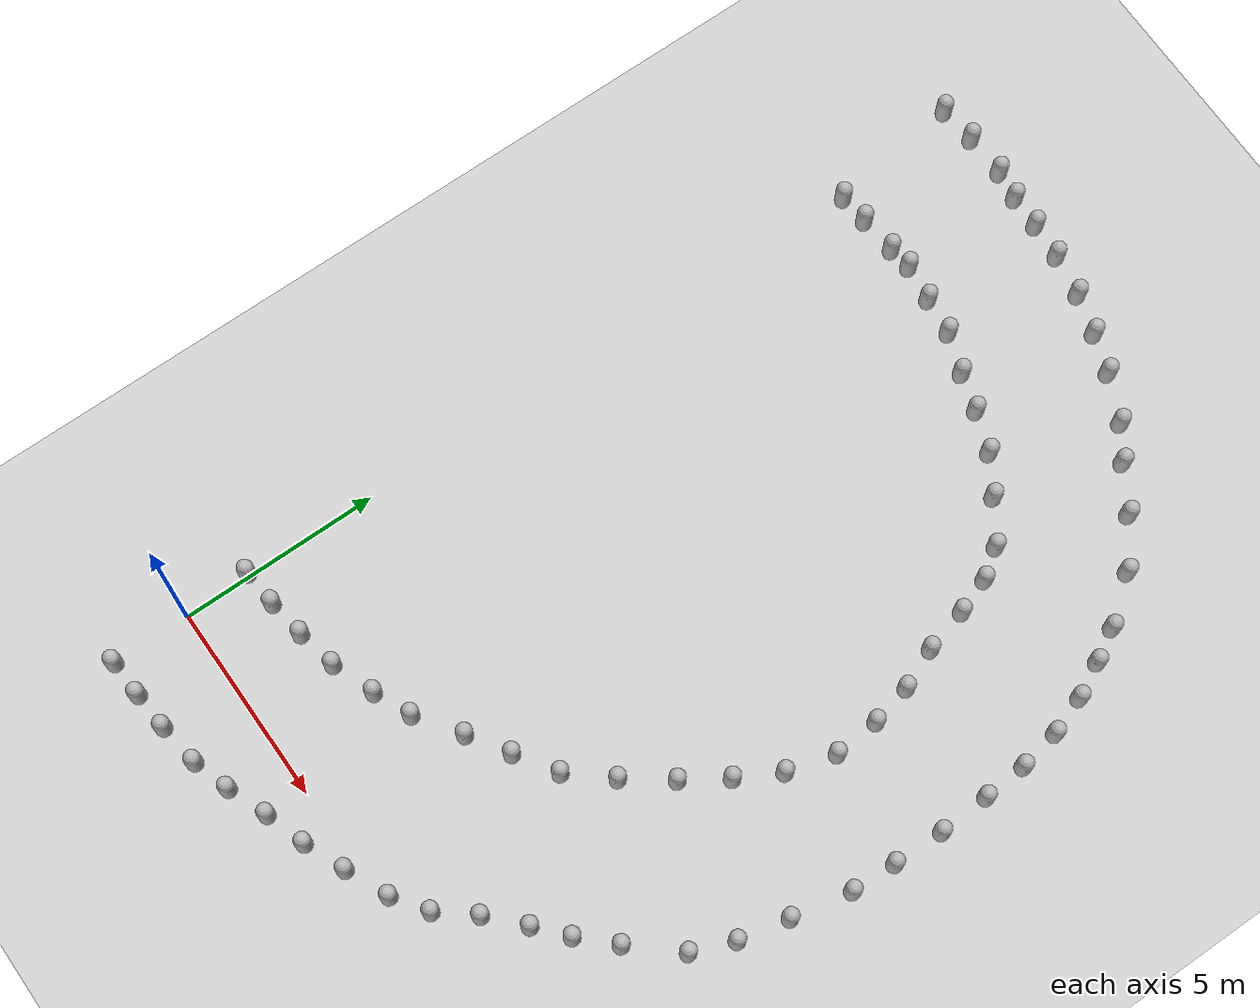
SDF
<sdf version='1.10'>
  <world name='empty'>
    <physics name='1ms' type='ignored'>
      <max_step_size>0.001</max_step_size>
      <real_time_factor>1</real_time_factor>
      <real_time_update_rate>1000</real_time_update_rate>
    </physics>
    <plugin name='gz::sim::systems::Physics' filename='gz-sim-physics-system'/>
    <plugin name='gz::sim::systems::UserCommands' filename='gz-sim-user-commands-system'/>
    <plugin name='gz::sim::systems::SceneBroadcaster' filename='gz-sim-scene-broadcaster-system'/>
    <plugin name='gz::sim::systems::Sensors' filename='gz-sim-sensors-system'>
      <render_engine>ogre2</render_engine>
    </plugin>
    <plugin name='gz::sim::systems::Contact' filename='gz-sim-contact-system'/>
    <gravity>0 0 -9.8000000000000007</gravity>
    <magnetic_field>5.5644999999999998e-06 2.2875799999999999e-05 -4.2388400000000002e-05</magnetic_field>
    <atmosphere type='adiabatic'/>
    <scene>
      <ambient>0.400000006 0.400000006 0.400000006 1</ambient>
      <background>0.699999988 0.699999988 0.699999988 1</background>
      <shadows>true</shadows>
    </scene>
    <model name='ground_plane'>
      <static>true</static>
      <link name='link'>
        <collision name='collision'>
          <geometry>
            <plane>
              <normal>0 0 1</normal>
              <size>100 100</size>
            </plane>
          </geometry>
          <surface>
            <friction>
              <ode/>
            </friction>
            <bounce/>
            <contact/>
          </surface>
        </collision>
        <visual name='visual'>
          <geometry>
            <plane>
              <normal>0 0 1</normal>
              <size>100 100</size>
            </plane>
          </geometry>
          <material>
            <ambient>0.800000012 0.800000012 0.800000012 1</ambient>
            <diffuse>0.800000012 0.800000012 0.800000012 1</diffuse>
            <specular>0.800000012 0.800000012 0.800000012 1</specular>
          </material>
        </visual>
        <pose>0 0 0 0 0 0</pose>
        <inertial>
          <pose>0 0 0 0 0 0</pose>
          <mass>1</mass>
          <inertia>
            <ixx>1</ixx>
            <ixy>0</ixy>
            <ixz>0</ixz>
            <iyy>1</iyy>
            <iyz>0</iyz>
            <izz>1</izz>
          </inertia>
        </inertial>
        <enable_wind>false</enable_wind>
      </link>
      <pose>0 0 0 0 0 0</pose>
      <self_collide>false</self_collide>
    </model>
    <model name='capsule'>
      <pose>0.0079092960798012868 1.6543923129827109 0.499999999902001 0 0 0</pose>
      <link name='capsule_link'>
        <inertial>
          <inertia>
            <ixx>0.074153999999999998</ixx>
            <ixy>0</ixy>
            <ixz>0</ixz>
            <iyy>0.074153999999999998</iyy>
            <iyz>0</iyz>
            <izz>0.018769000000000001</izz>
          </inertia>
          <mass>1</mass>
          <pose>0 0 0 0 0 0</pose>
        </inertial>
        <collision name='capsule_collision'>
          <geometry>
            <capsule>
              <radius>0.20000000000000001</radius>
              <length>0.59999999999999998</length>
            </capsule>
          </geometry>
          <surface>
            <friction>
              <ode/>
            </friction>
            <bounce/>
            <contact/>
          </surface>
        </collision>
        <visual name='capsule_visual'>
          <geometry>
            <capsule>
              <radius>0.20000000000000001</radius>
              <length>0.59999999999999998</length>
            </capsule>
          </geometry>
          <material>
            <ambient>0.300000012 0.300000012 0.300000012 1</ambient>
            <diffuse>0.699999988 0.699999988 0.699999988 1</diffuse>
            <specular>1 1 1 1</specular>
          </material>
        </visual>
        <pose>0 0 0 0 0 0</pose>
        <enable_wind>false</enable_wind>
      </link>
      <static>false</static>
      <self_collide>false</self_collide>
    </model>
    <model name='capsule_0'>
      <pose>0.94512511227716023 1.733680784439902 0.499999999902001 0 0 0</pose>
      <link name='capsule_link'>
        <inertial>
          <inertia>
            <ixx>0.074153999999999998</ixx>
            <ixy>0</ixy>
            <ixz>0</ixz>
            <iyy>0.074153999999999998</iyy>
            <iyz>0</iyz>
            <izz>0.018769000000000001</izz>
          </inertia>
          <mass>1</mass>
          <pose>0 0 0 0 0 0</pose>
        </inertial>
        <collision name='capsule_collision'>
          <geometry>
            <capsule>
              <radius>0.20000000000000001</radius>
              <length>0.59999999999999998</length>
            </capsule>
          </geometry>
          <surface>
            <friction>
              <ode/>
            </friction>
            <bounce/>
            <contact/>
          </surface>
        </collision>
        <visual name='capsule_visual'>
          <geometry>
            <capsule>
              <radius>0.20000000000000001</radius>
              <length>0.59999999999999998</length>
            </capsule>
          </geometry>
          <material>
            <ambient>0.300000012 0.300000012 0.300000012 1</ambient>
            <diffuse>0.699999988 0.699999988 0.699999988 1</diffuse>
            <specular>1 1 1 1</specular>
          </material>
        </visual>
        <pose>0 0 0 0 0 0</pose>
        <enable_wind>false</enable_wind>
      </link>
      <static>false</static>
      <self_collide>false</self_collide>
    </model>
    <model name='capsule_1'>
      <pose>1.9187066357914726 1.8748929251924817 0.499999999902001 0 0 0</pose>
      <link name='capsule_link'>
        <inertial>
          <inertia>
            <ixx>0.074153999999999998</ixx>
            <ixy>0</ixy>
            <ixz>0</ixz>
            <iyy>0.074153999999999998</iyy>
            <iyz>0</iyz>
            <izz>0.018769000000000001</izz>
          </inertia>
          <mass>1</mass>
          <pose>0 0 0 0 0 0</pose>
        </inertial>
        <collision name='capsule_collision'>
          <geometry>
            <capsule>
              <radius>0.20000000000000001</radius>
              <length>0.59999999999999998</length>
            </capsule>
          </geometry>
          <surface>
            <friction>
              <ode/>
            </friction>
            <bounce/>
            <contact/>
          </surface>
        </collision>
        <visual name='capsule_visual'>
          <geometry>
            <capsule>
              <radius>0.20000000000000001</radius>
              <length>0.59999999999999998</length>
            </capsule>
          </geometry>
          <material>
            <ambient>0.300000012 0.300000012 0.300000012 1</ambient>
            <diffuse>0.699999988 0.699999988 0.699999988 1</diffuse>
            <specular>1 1 1 1</specular>
          </material>
        </visual>
        <pose>0 0 0 0 0 0</pose>
        <enable_wind>false</enable_wind>
      </link>
      <static>false</static>
      <self_collide>false</self_collide>
    </model>
    <model name='capsule_2'>
      <pose>0.071174021114242758 -1.9452252499138223 0.499999999902001 0 0 0</pose>
      <link name='capsule_link'>
        <inertial>
          <inertia>
            <ixx>0.074153999999999998</ixx>
            <ixy>0</ixy>
            <ixz>0</ixz>
            <iyy>0.074153999999999998</iyy>
            <iyz>0</iyz>
            <izz>0.018769000000000001</izz>
          </inertia>
          <mass>1</mass>
          <pose>0 0 0 0 0 0</pose>
        </inertial>
        <collision name='capsule_collision'>
          <geometry>
            <capsule>
              <radius>0.20000000000000001</radius>
              <length>0.59999999999999998</length>
            </capsule>
          </geometry>
          <surface>
            <friction>
              <ode/>
            </friction>
            <bounce/>
            <contact/>
          </surface>
        </collision>
        <visual name='capsule_visual'>
          <geometry>
            <capsule>
              <radius>0.20000000000000001</radius>
              <length>0.59999999999999998</length>
            </capsule>
          </geometry>
          <material>
            <ambient>0.300000012 0.300000012 0.300000012 1</ambient>
            <diffuse>0.699999988 0.699999988 0.699999988 1</diffuse>
            <specular>1 1 1 1</specular>
          </material>
        </visual>
        <pose>0 0 0 0 0 0</pose>
        <enable_wind>false</enable_wind>
      </link>
      <static>false</static>
      <self_collide>false</self_collide>
    </model>
    <model name='capsule_3'>
      <pose>1.0079840875515076 -1.8969727998720727 0.499999999902001 0 0 0</pose>
      <link name='capsule_link'>
        <inertial>
          <inertia>
            <ixx>0.074153999999999998</ixx>
            <ixy>0</ixy>
            <ixz>0</ixz>
            <iyy>0.074153999999999998</iyy>
            <iyz>0</iyz>
            <izz>0.018769000000000001</izz>
          </inertia>
          <mass>1</mass>
          <pose>0 0 0 0 0 0</pose>
        </inertial>
        <collision name='capsule_collision'>
          <geometry>
            <capsule>
              <radius>0.20000000000000001</radius>
              <length>0.59999999999999998</length>
            </capsule>
          </geometry>
          <surface>
            <friction>
              <ode/>
            </friction>
            <bounce/>
            <contact/>
          </surface>
        </collision>
        <visual name='capsule_visual'>
          <geometry>
            <capsule>
              <radius>0.20000000000000001</radius>
              <length>0.59999999999999998</length>
            </capsule>
          </geometry>
          <material>
            <ambient>0.300000012 0.300000012 0.300000012 1</ambient>
            <diffuse>0.699999988 0.699999988 0.699999988 1</diffuse>
            <specular>1 1 1 1</specular>
          </material>
        </visual>
        <pose>0 0 0 0 0 0</pose>
        <enable_wind>false</enable_wind>
      </link>
      <static>false</static>
      <self_collide>false</self_collide>
    </model>
    <model name='capsule_4'>
      <pose>1.9770966511890031 -1.8243848592570489 0.499999999902001 0 0 0</pose>
      <link name='capsule_link'>
        <inertial>
          <inertia>
            <ixx>0.074153999999999998</ixx>
            <ixy>0</ixy>
            <ixz>0</ixz>
            <iyy>0.074153999999999998</iyy>
            <iyz>0</iyz>
            <izz>0.018769000000000001</izz>
          </inertia>
          <mass>1</mass>
          <pose>0 0 0 0 0 0</pose>
        </inertial>
        <collision name='capsule_collision'>
          <geometry>
            <capsule>
              <radius>0.20000000000000001</radius>
              <length>0.59999999999999998</length>
            </capsule>
          </geometry>
          <surface>
            <friction>
              <ode/>
            </friction>
            <bounce/>
            <contact/>
          </surface>
        </collision>
        <visual name='capsule_visual'>
          <geometry>
            <capsule>
              <radius>0.20000000000000001</radius>
              <length>0.59999999999999998</length>
            </capsule>
          </geometry>
          <material>
            <ambient>0.300000012 0.300000012 0.300000012 1</ambient>
            <diffuse>0.699999988 0.699999988 0.699999988 1</diffuse>
            <specular>1 1 1 1</specular>
          </material>
        </visual>
        <pose>0 0 0 0 0 0</pose>
        <enable_wind>false</enable_wind>
      </link>
      <static>false</static>
      <self_collide>false</self_collide>
    </model>
    <model name='capsule_5'>
      <pose>2.9418799014673973 2.0835173150101385 0.499999999902001 0 0 0</pose>
      <link name='capsule_link'>
        <inertial>
          <inertia>
            <ixx>0.074153999999999998</ixx>
            <ixy>0</ixy>
            <ixz>0</ixz>
            <iyy>0.074153999999999998</iyy>
            <iyz>0</iyz>
            <izz>0.018769000000000001</izz>
          </inertia>
          <mass>1</mass>
          <pose>0 0 0 0 0 0</pose>
        </inertial>
        <collision name='capsule_collision'>
          <geometry>
            <capsule>
              <radius>0.20000000000000001</radius>
              <length>0.59999999999999998</length>
            </capsule>
          </geometry>
          <surface>
            <friction>
              <ode/>
            </friction>
            <bounce/>
            <contact/>
          </surface>
        </collision>
        <visual name='capsule_visual'>
          <geometry>
            <capsule>
              <radius>0.20000000000000001</radius>
              <length>0.59999999999999998</length>
            </capsule>
          </geometry>
          <material>
            <ambient>0.300000012 0.300000012 0.300000012 1</ambient>
            <diffuse>0.699999988 0.699999988 0.699999988 1</diffuse>
            <specular>1 1 1 1</specular>
          </material>
        </visual>
        <pose>0 0 0 0 0 0</pose>
        <enable_wind>false</enable_wind>
      </link>
      <static>false</static>
      <self_collide>false</self_collide>
    </model>
    <model name='capsule_6'>
      <pose>3.0534784039541742 -1.6741857712264725 0.499999999902001 0 0 0</pose>
      <link name='capsule_link'>
        <inertial>
          <inertia>
            <ixx>0.074153999999999998</ixx>
            <ixy>0</ixy>
            <ixz>0</ixz>
            <iyy>0.074153999999999998</iyy>
            <iyz>0</iyz>
            <izz>0.018769000000000001</izz>
          </inertia>
          <mass>1</mass>
          <pose>0 0 0 0 0 0</pose>
        </inertial>
        <collision name='capsule_collision'>
          <geometry>
            <capsule>
              <radius>0.20000000000000001</radius>
              <length>0.59999999999999998</length>
            </capsule>
          </geometry>
          <surface>
            <friction>
              <ode/>
            </friction>
            <bounce/>
            <contact/>
          </surface>
        </collision>
        <visual name='capsule_visual'>
          <geometry>
            <capsule>
              <radius>0.20000000000000001</radius>
              <length>0.59999999999999998</length>
            </capsule>
          </geometry>
          <material>
            <ambient>0.300000012 0.300000012 0.300000012 1</ambient>
            <diffuse>0.699999988 0.699999988 0.699999988 1</diffuse>
            <specular>1 1 1 1</specular>
          </material>
        </visual>
        <pose>0 0 0 0 0 0</pose>
        <enable_wind>false</enable_wind>
      </link>
      <static>false</static>
      <self_collide>false</self_collide>
    </model>
    <model name='capsule_7'>
      <pose>4.0094379070136714 2.4839232532498823 0.499999999902001 0 0 0</pose>
      <link name='capsule_link'>
        <inertial>
          <inertia>
            <ixx>0.074153999999999998</ixx>
            <ixy>0</ixy>
            <ixz>0</ixz>
            <iyy>0.074153999999999998</iyy>
            <iyz>0</iyz>
            <izz>0.018769000000000001</izz>
          </inertia>
          <mass>1</mass>
          <pose>0 0 0 0 0 0</pose>
        </inertial>
        <collision name='capsule_collision'>
          <geometry>
            <capsule>
              <radius>0.20000000000000001</radius>
              <length>0.59999999999999998</length>
            </capsule>
          </geometry>
          <surface>
            <friction>
              <ode/>
            </friction>
            <bounce/>
            <contact/>
          </surface>
        </collision>
        <visual name='capsule_visual'>
          <geometry>
            <capsule>
              <radius>0.20000000000000001</radius>
              <length>0.59999999999999998</length>
            </capsule>
          </geometry>
          <material>
            <ambient>0.300000012 0.300000012 0.300000012 1</ambient>
            <diffuse>0.699999988 0.699999988 0.699999988 1</diffuse>
            <specular>1 1 1 1</specular>
          </material>
        </visual>
        <pose>0 0 0 0 0 0</pose>
        <enable_wind>false</enable_wind>
      </link>
      <static>false</static>
      <self_collide>false</self_collide>
    </model>
    <model name='capsule_8'>
      <pose>3.9933107917520312 -1.3831246201174401 0.499999999902001 0 0 0</pose>
      <link name='capsule_link'>
        <inertial>
          <inertia>
            <ixx>0.074153999999999998</ixx>
            <ixy>0</ixy>
            <ixz>0</ixz>
            <iyy>0.074153999999999998</iyy>
            <iyz>0</iyz>
            <izz>0.018769000000000001</izz>
          </inertia>
          <mass>1</mass>
          <pose>0 0 0 0 0 0</pose>
        </inertial>
        <collision name='capsule_collision'>
          <geometry>
            <capsule>
              <radius>0.20000000000000001</radius>
              <length>0.59999999999999998</length>
            </capsule>
          </geometry>
          <surface>
            <friction>
              <ode/>
            </friction>
            <bounce/>
            <contact/>
          </surface>
        </collision>
        <visual name='capsule_visual'>
          <geometry>
            <capsule>
              <radius>0.20000000000000001</radius>
              <length>0.59999999999999998</length>
            </capsule>
          </geometry>
          <material>
            <ambient>0.300000012 0.300000012 0.300000012 1</ambient>
            <diffuse>0.699999988 0.699999988 0.699999988 1</diffuse>
            <specular>1 1 1 1</specular>
          </material>
        </visual>
        <pose>0 0 0 0 0 0</pose>
        <enable_wind>false</enable_wind>
      </link>
      <static>false</static>
      <self_collide>false</self_collide>
    </model>
    <model name='capsule_9'>
      <pose>4.9272845839928587 2.8907733621151106 0.499999999902001 0 0 0</pose>
      <link name='capsule_link'>
        <inertial>
          <inertia>
            <ixx>0.074153999999999998</ixx>
            <ixy>0</ixy>
            <ixz>0</ixz>
            <iyy>0.074153999999999998</iyy>
            <iyz>0</iyz>
            <izz>0.018769000000000001</izz>
          </inertia>
          <mass>1</mass>
          <pose>0 0 0 0 0 0</pose>
        </inertial>
        <collision name='capsule_collision'>
          <geometry>
            <capsule>
              <radius>0.20000000000000001</radius>
              <length>0.59999999999999998</length>
            </capsule>
          </geometry>
          <surface>
            <friction>
              <ode/>
            </friction>
            <bounce/>
            <contact/>
          </surface>
        </collision>
        <visual name='capsule_visual'>
          <geometry>
            <capsule>
              <radius>0.20000000000000001</radius>
              <length>0.59999999999999998</length>
            </capsule>
          </geometry>
          <material>
            <ambient>0.300000012 0.300000012 0.300000012 1</ambient>
            <diffuse>0.699999988 0.699999988 0.699999988 1</diffuse>
            <specular>1 1 1 1</specular>
          </material>
        </visual>
        <pose>0 0 0 0 0 0</pose>
        <enable_wind>false</enable_wind>
      </link>
      <static>false</static>
      <self_collide>false</self_collide>
    </model>
    <model name='capsule_10'>
      <pose>4.9840762807257226 -0.98658179176943239 0.499999999902001 0 0 0</pose>
      <link name='capsule_link'>
        <inertial>
          <inertia>
            <ixx>0.074153999999999998</ixx>
            <ixy>0</ixy>
            <ixz>0</ixz>
            <iyy>0.074153999999999998</iyy>
            <iyz>0</iyz>
            <izz>0.018769000000000001</izz>
          </inertia>
          <mass>1</mass>
          <pose>0 0 0 0 0 0</pose>
        </inertial>
        <collision name='capsule_collision'>
          <geometry>
            <capsule>
              <radius>0.20000000000000001</radius>
              <length>0.59999999999999998</length>
            </capsule>
          </geometry>
          <surface>
            <friction>
              <ode/>
            </friction>
            <bounce/>
            <contact/>
          </surface>
        </collision>
        <visual name='capsule_visual'>
          <geometry>
            <capsule>
              <radius>0.20000000000000001</radius>
              <length>0.59999999999999998</length>
            </capsule>
          </geometry>
          <material>
            <ambient>0.300000012 0.300000012 0.300000012 1</ambient>
            <diffuse>0.699999988 0.699999988 0.699999988 1</diffuse>
            <specular>1 1 1 1</specular>
          </material>
        </visual>
        <pose>0 0 0 0 0 0</pose>
        <enable_wind>false</enable_wind>
      </link>
      <static>false</static>
      <self_collide>false</self_collide>
    </model>
    <model name='capsule_11'>
      <pose>5.9982967455937626 3.6300361546412354 0.499999999902001 0 0 0</pose>
      <link name='capsule_link'>
        <inertial>
          <inertia>
            <ixx>0.074153999999999998</ixx>
            <ixy>0</ixy>
            <ixz>0</ixz>
            <iyy>0.074153999999999998</iyy>
            <iyz>0</iyz>
            <izz>0.018769000000000001</izz>
          </inertia>
          <mass>1</mass>
          <pose>0 0 0 0 0 0</pose>
        </inertial>
        <collision name='capsule_collision'>
          <geometry>
            <capsule>
              <radius>0.20000000000000001</radius>
              <length>0.59999999999999998</length>
            </capsule>
          </geometry>
          <surface>
            <friction>
              <ode/>
            </friction>
            <bounce/>
            <contact/>
          </surface>
        </collision>
        <visual name='capsule_visual'>
          <geometry>
            <capsule>
              <radius>0.20000000000000001</radius>
              <length>0.59999999999999998</length>
            </capsule>
          </geometry>
          <material>
            <ambient>0.300000012 0.300000012 0.300000012 1</ambient>
            <diffuse>0.699999988 0.699999988 0.699999988 1</diffuse>
            <specular>1 1 1 1</specular>
          </material>
        </visual>
        <pose>0 0 0 0 0 0</pose>
        <enable_wind>false</enable_wind>
      </link>
      <static>false</static>
      <self_collide>false</self_collide>
    </model>
    <model name='capsule_12'>
      <pose>5.9997241077704127 -0.66053042265015316 0.499999999902001 0 0 0</pose>
      <link name='capsule_link'>
        <inertial>
          <inertia>
            <ixx>0.074153999999999998</ixx>
            <ixy>0</ixy>
            <ixz>0</ixz>
            <iyy>0.074153999999999998</iyy>
            <iyz>0</iyz>
            <izz>0.018769000000000001</izz>
          </inertia>
          <mass>1</mass>
          <pose>0 0 0 0 0 0</pose>
        </inertial>
        <collision name='capsule_collision'>
          <geometry>
            <capsule>
              <radius>0.20000000000000001</radius>
              <length>0.59999999999999998</length>
            </capsule>
          </geometry>
          <surface>
            <friction>
              <ode/>
            </friction>
            <bounce/>
            <contact/>
          </surface>
        </collision>
        <visual name='capsule_visual'>
          <geometry>
            <capsule>
              <radius>0.20000000000000001</radius>
              <length>0.59999999999999998</length>
            </capsule>
          </geometry>
          <material>
            <ambient>0.300000012 0.300000012 0.300000012 1</ambient>
            <diffuse>0.699999988 0.699999988 0.699999988 1</diffuse>
            <specular>1 1 1 1</specular>
          </material>
        </visual>
        <pose>0 0 0 0 0 0</pose>
        <enable_wind>false</enable_wind>
      </link>
      <static>false</static>
      <self_collide>false</self_collide>
    </model>
    <model name='capsule_13'>
      <pose>6.9596569506124863 4.2527939600757358 0.499999999902001 0 0 0</pose>
      <link name='capsule_link'>
        <inertial>
          <inertia>
            <ixx>0.074153999999999998</ixx>
            <ixy>0</ixy>
            <ixz>0</ixz>
            <iyy>0.074153999999999998</iyy>
            <iyz>0</iyz>
            <izz>0.018769000000000001</izz>
          </inertia>
          <mass>1</mass>
          <pose>0 0 0 0 0 0</pose>
        </inertial>
        <collision name='capsule_collision'>
          <geometry>
            <capsule>
              <radius>0.20000000000000001</radius>
              <length>0.59999999999999998</length>
            </capsule>
          </geometry>
          <surface>
            <friction>
              <ode/>
            </friction>
            <bounce/>
            <contact/>
          </surface>
        </collision>
        <visual name='capsule_visual'>
          <geometry>
            <capsule>
              <radius>0.20000000000000001</radius>
              <length>0.59999999999999998</length>
            </capsule>
          </geometry>
          <material>
            <ambient>0.300000012 0.300000012 0.300000012 1</ambient>
            <diffuse>0.699999988 0.699999988 0.699999988 1</diffuse>
            <specular>1 1 1 1</specular>
          </material>
        </visual>
        <pose>0 0 0 0 0 0</pose>
        <enable_wind>false</enable_wind>
      </link>
      <static>false</static>
      <self_collide>false</self_collide>
    </model>
    <model name='capsule_14'>
      <pose>7.0108881171063908 -0.23596897892512203 0.499999999902001 0 0 0</pose>
      <link name='capsule_link'>
        <inertial>
          <inertia>
            <ixx>0.074153999999999998</ixx>
            <ixy>0</ixy>
            <ixz>0</ixz>
            <iyy>0.074153999999999998</iyy>
            <iyz>0</iyz>
            <izz>0.018769000000000001</izz>
          </inertia>
          <mass>1</mass>
          <pose>0 0 0 0 0 0</pose>
        </inertial>
        <collision name='capsule_collision'>
          <geometry>
            <capsule>
              <radius>0.20000000000000001</radius>
              <length>0.59999999999999998</length>
            </capsule>
          </geometry>
          <surface>
            <friction>
              <ode/>
            </friction>
            <bounce/>
            <contact/>
          </surface>
        </collision>
        <visual name='capsule_visual'>
          <geometry>
            <capsule>
              <radius>0.20000000000000001</radius>
              <length>0.59999999999999998</length>
            </capsule>
          </geometry>
          <material>
            <ambient>0.300000012 0.300000012 0.300000012 1</ambient>
            <diffuse>0.699999988 0.699999988 0.699999988 1</diffuse>
            <specular>1 1 1 1</specular>
          </material>
        </visual>
        <pose>0 0 0 0 0 0</pose>
        <enable_wind>false</enable_wind>
      </link>
      <static>false</static>
      <self_collide>false</self_collide>
    </model>
    <model name='capsule_15'>
      <pose>7.9441173175420836 4.8912118331948875 0.499999999902001 0 0 0</pose>
      <link name='capsule_link'>
        <inertial>
          <inertia>
            <ixx>0.074153999999999998</ixx>
            <ixy>0</ixy>
            <ixz>0</ixz>
            <iyy>0.074153999999999998</iyy>
            <iyz>0</iyz>
            <izz>0.018769000000000001</izz>
          </inertia>
          <mass>1</mass>
          <pose>0 0 0 0 0 0</pose>
        </inertial>
        <collision name='capsule_collision'>
          <geometry>
            <capsule>
              <radius>0.20000000000000001</radius>
              <length>0.59999999999999998</length>
            </capsule>
          </geometry>
          <surface>
            <friction>
              <ode/>
            </friction>
            <bounce/>
            <contact/>
          </surface>
        </collision>
        <visual name='capsule_visual'>
          <geometry>
            <capsule>
              <radius>0.20000000000000001</radius>
              <length>0.59999999999999998</length>
            </capsule>
          </geometry>
          <material>
            <ambient>0.300000012 0.300000012 0.300000012 1</ambient>
            <diffuse>0.699999988 0.699999988 0.699999988 1</diffuse>
            <specular>1 1 1 1</specular>
          </material>
        </visual>
        <pose>0 0 0 0 0 0</pose>
        <enable_wind>false</enable_wind>
      </link>
      <static>false</static>
      <self_collide>false</self_collide>
    </model>
    <model name='capsule_16'>
      <pose>8.0572184014874164 0.23701005670510478 0.499999999902001 0 0 0</pose>
      <link name='capsule_link'>
        <inertial>
          <inertia>
            <ixx>0.074153999999999998</ixx>
            <ixy>0</ixy>
            <ixz>0</ixz>
            <iyy>0.074153999999999998</iyy>
            <iyz>0</iyz>
            <izz>0.018769000000000001</izz>
          </inertia>
          <mass>1</mass>
          <pose>0 0 0 0 0 0</pose>
        </inertial>
        <collision name='capsule_collision'>
          <geometry>
            <capsule>
              <radius>0.20000000000000001</radius>
              <length>0.59999999999999998</length>
            </capsule>
          </geometry>
          <surface>
            <friction>
              <ode/>
            </friction>
            <bounce/>
            <contact/>
          </surface>
        </collision>
        <visual name='capsule_visual'>
          <geometry>
            <capsule>
              <radius>0.20000000000000001</radius>
              <length>0.59999999999999998</length>
            </capsule>
          </geometry>
          <material>
            <ambient>0.300000012 0.300000012 0.300000012 1</ambient>
            <diffuse>0.699999988 0.699999988 0.699999988 1</diffuse>
            <specular>1 1 1 1</specular>
          </material>
        </visual>
        <pose>0 0 0 0 0 0</pose>
        <enable_wind>false</enable_wind>
      </link>
      <static>false</static>
      <self_collide>false</self_collide>
    </model>
    <model name='capsule_17'>
      <pose>8.784491633246251 5.8662201830098777 0.499999999902001 0 0 0</pose>
      <link name='capsule_link'>
        <inertial>
          <inertia>
            <ixx>0.074153999999999998</ixx>
            <ixy>0</ixy>
            <ixz>0</ixz>
            <iyy>0.074153999999999998</iyy>
            <iyz>0</iyz>
            <izz>0.018769000000000001</izz>
          </inertia>
          <mass>1</mass>
          <pose>0 0 0 0 0 0</pose>
        </inertial>
        <collision name='capsule_collision'>
          <geometry>
            <capsule>
              <radius>0.20000000000000001</radius>
              <length>0.59999999999999998</length>
            </capsule>
          </geometry>
          <surface>
            <friction>
              <ode/>
            </friction>
            <bounce/>
            <contact/>
          </surface>
        </collision>
        <visual name='capsule_visual'>
          <geometry>
            <capsule>
              <radius>0.20000000000000001</radius>
              <length>0.59999999999999998</length>
            </capsule>
          </geometry>
          <material>
            <ambient>0.300000012 0.300000012 0.300000012 1</ambient>
            <diffuse>0.699999988 0.699999988 0.699999988 1</diffuse>
            <specular>1 1 1 1</specular>
          </material>
        </visual>
        <pose>0 0 0 0 0 0</pose>
        <enable_wind>false</enable_wind>
      </link>
      <static>false</static>
      <self_collide>false</self_collide>
    </model>
    <model name='capsule_18'>
      <pose>8.8740413969647456 0.80734262371132193 0.499999999902001 0 0 0</pose>
      <link name='capsule_link'>
        <inertial>
          <inertia>
            <ixx>0.074153999999999998</ixx>
            <ixy>0</ixy>
            <ixz>0</ixz>
            <iyy>0.074153999999999998</iyy>
            <iyz>0</iyz>
            <izz>0.018769000000000001</izz>
          </inertia>
          <mass>1</mass>
          <pose>0 0 0 0 0 0</pose>
        </inertial>
        <collision name='capsule_collision'>
          <geometry>
            <capsule>
              <radius>0.20000000000000001</radius>
              <length>0.59999999999999998</length>
            </capsule>
          </geometry>
          <surface>
            <friction>
              <ode/>
            </friction>
            <bounce/>
            <contact/>
          </surface>
        </collision>
        <visual name='capsule_visual'>
          <geometry>
            <capsule>
              <radius>0.20000000000000001</radius>
              <length>0.59999999999999998</length>
            </capsule>
          </geometry>
          <material>
            <ambient>0.300000012 0.300000012 0.300000012 1</ambient>
            <diffuse>0.699999988 0.699999988 0.699999988 1</diffuse>
            <specular>1 1 1 1</specular>
          </material>
        </visual>
        <pose>0 0 0 0 0 0</pose>
        <enable_wind>false</enable_wind>
      </link>
      <static>false</static>
      <self_collide>false</self_collide>
    </model>
    <model name='capsule_19'>
      <pose>9.565480298544724 1.6502451150646742 0.499999999902001 0 0 0</pose>
      <link name='capsule_link'>
        <inertial>
          <inertia>
            <ixx>0.074153999999999998</ixx>
            <ixy>0</ixy>
            <ixz>0</ixz>
            <iyy>0.074153999999999998</iyy>
            <iyz>0</iyz>
            <izz>0.018769000000000001</izz>
          </inertia>
          <mass>1</mass>
          <pose>0 0 0 0 0 0</pose>
        </inertial>
        <collision name='capsule_collision'>
          <geometry>
            <capsule>
              <radius>0.20000000000000001</radius>
              <length>0.59999999999999998</length>
            </capsule>
          </geometry>
          <surface>
            <friction>
              <ode/>
            </friction>
            <bounce/>
            <contact/>
          </surface>
        </collision>
        <visual name='capsule_visual'>
          <geometry>
            <capsule>
              <radius>0.20000000000000001</radius>
              <length>0.59999999999999998</length>
            </capsule>
          </geometry>
          <material>
            <ambient>0.300000012 0.300000012 0.300000012 1</ambient>
            <diffuse>0.699999988 0.699999988 0.699999988 1</diffuse>
            <specular>1 1 1 1</specular>
          </material>
        </visual>
        <pose>0 0 0 0 0 0</pose>
        <enable_wind>false</enable_wind>
      </link>
      <static>false</static>
      <self_collide>false</self_collide>
    </model>
    <model name='capsule_20'>
      <pose>9.5760287630693099 6.9376943894907726 0.499999999902001 0 0 0</pose>
      <link name='capsule_link'>
        <inertial>
          <inertia>
            <ixx>0.074153999999999998</ixx>
            <ixy>0</ixy>
            <ixz>0</ixz>
            <iyy>0.074153999999999998</iyy>
            <iyz>0</iyz>
            <izz>0.018769000000000001</izz>
          </inertia>
          <mass>1</mass>
          <pose>0 0 0 0 0 0</pose>
        </inertial>
        <collision name='capsule_collision'>
          <geometry>
            <capsule>
              <radius>0.20000000000000001</radius>
              <length>0.59999999999999998</length>
            </capsule>
          </geometry>
          <surface>
            <friction>
              <ode/>
            </friction>
            <bounce/>
            <contact/>
          </surface>
        </collision>
        <visual name='capsule_visual'>
          <geometry>
            <capsule>
              <radius>0.20000000000000001</radius>
              <length>0.59999999999999998</length>
            </capsule>
          </geometry>
          <material>
            <ambient>0.300000012 0.300000012 0.300000012 1</ambient>
            <diffuse>0.699999988 0.699999988 0.699999988 1</diffuse>
            <specular>1 1 1 1</specular>
          </material>
        </visual>
        <pose>0 0 0 0 0 0</pose>
        <enable_wind>false</enable_wind>
      </link>
      <static>false</static>
      <self_collide>false</self_collide>
    </model>
    <model name='capsule_21'>
      <pose>10.381177677795568 2.4105502564392642 0.499999999902001 0 0 0</pose>
      <link name='capsule_link'>
        <inertial>
          <inertia>
            <ixx>0.074153999999999998</ixx>
            <ixy>0</ixy>
            <ixz>0</ixz>
            <iyy>0.074153999999999998</iyy>
            <iyz>0</iyz>
            <izz>0.018769000000000001</izz>
          </inertia>
          <mass>1</mass>
          <pose>0 0 0 0 0 0</pose>
        </inertial>
        <collision name='capsule_collision'>
          <geometry>
            <capsule>
              <radius>0.20000000000000001</radius>
              <length>0.59999999999999998</length>
            </capsule>
          </geometry>
          <surface>
            <friction>
              <ode/>
            </friction>
            <bounce/>
            <contact/>
          </surface>
        </collision>
        <visual name='capsule_visual'>
          <geometry>
            <capsule>
              <radius>0.20000000000000001</radius>
              <length>0.59999999999999998</length>
            </capsule>
          </geometry>
          <material>
            <ambient>0.300000012 0.300000012 0.300000012 1</ambient>
            <diffuse>0.699999988 0.699999988 0.699999988 1</diffuse>
            <specular>1 1 1 1</specular>
          </material>
        </visual>
        <pose>0 0 0 0 0 0</pose>
        <enable_wind>false</enable_wind>
      </link>
      <static>false</static>
      <self_collide>false</self_collide>
    </model>
    <model name='capsule_22'>
      <pose>11.104713062926447 3.0382462982686742 0.499999999902001 0 0 0</pose>
      <link name='capsule_link'>
        <inertial>
          <inertia>
            <ixx>0.074153999999999998</ixx>
            <ixy>0</ixy>
            <ixz>0</ixz>
            <iyy>0.074153999999999998</iyy>
            <iyz>0</iyz>
            <izz>0.018769000000000001</izz>
          </inertia>
          <mass>1</mass>
          <pose>0 0 0 0 0 0</pose>
        </inertial>
        <collision name='capsule_collision'>
          <geometry>
            <capsule>
              <radius>0.20000000000000001</radius>
              <length>0.59999999999999998</length>
            </capsule>
          </geometry>
          <surface>
            <friction>
              <ode/>
            </friction>
            <bounce/>
            <contact/>
          </surface>
        </collision>
        <visual name='capsule_visual'>
          <geometry>
            <capsule>
              <radius>0.20000000000000001</radius>
              <length>0.59999999999999998</length>
            </capsule>
          </geometry>
          <material>
            <ambient>0.300000012 0.300000012 0.300000012 1</ambient>
            <diffuse>0.699999988 0.699999988 0.699999988 1</diffuse>
            <specular>1 1 1 1</specular>
          </material>
        </visual>
        <pose>0 0 0 0 0 0</pose>
        <enable_wind>false</enable_wind>
      </link>
      <static>false</static>
      <self_collide>false</self_collide>
    </model>
    <model name='capsule_23'>
      <pose>11.863521378822202 3.8158140797079758 0.499999999902001 0 0 0</pose>
      <link name='capsule_link'>
        <inertial>
          <inertia>
            <ixx>0.074153999999999998</ixx>
            <ixy>0</ixy>
            <ixz>0</ixz>
            <iyy>0.074153999999999998</iyy>
            <iyz>0</iyz>
            <izz>0.018769000000000001</izz>
          </inertia>
          <mass>1</mass>
          <pose>0 0 0 0 0 0</pose>
        </inertial>
        <collision name='capsule_collision'>
          <geometry>
            <capsule>
              <radius>0.20000000000000001</radius>
              <length>0.59999999999999998</length>
            </capsule>
          </geometry>
          <surface>
            <friction>
              <ode/>
            </friction>
            <bounce/>
            <contact/>
          </surface>
        </collision>
        <visual name='capsule_visual'>
          <geometry>
            <capsule>
              <radius>0.20000000000000001</radius>
              <length>0.59999999999999998</length>
            </capsule>
          </geometry>
          <material>
            <ambient>0.300000012 0.300000012 0.300000012 1</ambient>
            <diffuse>0.699999988 0.699999988 0.699999988 1</diffuse>
            <specular>1 1 1 1</specular>
          </material>
        </visual>
        <pose>0 0 0 0 0 0</pose>
        <enable_wind>false</enable_wind>
      </link>
      <static>false</static>
      <self_collide>false</self_collide>
    </model>
    <model name='capsule_24'>
      <pose>12.842624452844444 4.9232899690504173 0.499999999902001 0 0 0</pose>
      <link name='capsule_link'>
        <inertial>
          <inertia>
            <ixx>0.074153999999999998</ixx>
            <ixy>0</ixy>
            <ixz>0</ixz>
            <iyy>0.074153999999999998</iyy>
            <iyz>0</iyz>
            <izz>0.018769000000000001</izz>
          </inertia>
          <mass>1</mass>
          <pose>0 0 0 0 0 0</pose>
        </inertial>
        <collision name='capsule_collision'>
          <geometry>
            <capsule>
              <radius>0.20000000000000001</radius>
              <length>0.59999999999999998</length>
            </capsule>
          </geometry>
          <surface>
            <friction>
              <ode/>
            </friction>
            <bounce/>
            <contact/>
          </surface>
        </collision>
        <visual name='capsule_visual'>
          <geometry>
            <capsule>
              <radius>0.20000000000000001</radius>
              <length>0.59999999999999998</length>
            </capsule>
          </geometry>
          <material>
            <ambient>0.300000012 0.300000012 0.300000012 1</ambient>
            <diffuse>0.699999988 0.699999988 0.699999988 1</diffuse>
            <specular>1 1 1 1</specular>
          </material>
        </visual>
        <pose>0 0 0 0 0 0</pose>
        <enable_wind>false</enable_wind>
      </link>
      <static>false</static>
      <self_collide>false</self_collide>
    </model>
    <model name='capsule_25'>
      <pose>10.241065206843952 7.968432308927837 0.499999999902001 0 0 0</pose>
      <link name='capsule_link'>
        <inertial>
          <inertia>
            <ixx>0.074153999999999998</ixx>
            <ixy>0</ixy>
            <ixz>0</ixz>
            <iyy>0.074153999999999998</iyy>
            <iyz>0</iyz>
            <izz>0.018769000000000001</izz>
          </inertia>
          <mass>1</mass>
          <pose>0 0 0 0 0 0</pose>
        </inertial>
        <collision name='capsule_collision'>
          <geometry>
            <capsule>
              <radius>0.20000000000000001</radius>
              <length>0.59999999999999998</length>
            </capsule>
          </geometry>
          <surface>
            <friction>
              <ode/>
            </friction>
            <bounce/>
            <contact/>
          </surface>
        </collision>
        <visual name='capsule_visual'>
          <geometry>
            <capsule>
              <radius>0.20000000000000001</radius>
              <length>0.59999999999999998</length>
            </capsule>
          </geometry>
          <material>
            <ambient>0.300000012 0.300000012 0.300000012 1</ambient>
            <diffuse>0.699999988 0.699999988 0.699999988 1</diffuse>
            <specular>1 1 1 1</specular>
          </material>
        </visual>
        <pose>0 0 0 0 0 0</pose>
        <enable_wind>false</enable_wind>
      </link>
      <static>false</static>
      <self_collide>false</self_collide>
    </model>
    <model name='capsule_26'>
      <pose>10.799237430340604 9.0142262635759707 0.499999999902001 0 0 0</pose>
      <link name='capsule_link'>
        <inertial>
          <inertia>
            <ixx>0.074153999999999998</ixx>
            <ixy>0</ixy>
            <ixz>0</ixz>
            <iyy>0.074153999999999998</iyy>
            <iyz>0</iyz>
            <izz>0.018769000000000001</izz>
          </inertia>
          <mass>1</mass>
          <pose>0 0 0 0 0 0</pose>
        </inertial>
        <collision name='capsule_collision'>
          <geometry>
            <capsule>
              <radius>0.20000000000000001</radius>
              <length>0.59999999999999998</length>
            </capsule>
          </geometry>
          <surface>
            <friction>
              <ode/>
            </friction>
            <bounce/>
            <contact/>
          </surface>
        </collision>
        <visual name='capsule_visual'>
          <geometry>
            <capsule>
              <radius>0.20000000000000001</radius>
              <length>0.59999999999999998</length>
            </capsule>
          </geometry>
          <material>
            <ambient>0.300000012 0.300000012 0.300000012 1</ambient>
            <diffuse>0.699999988 0.699999988 0.699999988 1</diffuse>
            <specular>1 1 1 1</specular>
          </material>
        </visual>
        <pose>0 0 0 0 0 0</pose>
        <enable_wind>false</enable_wind>
      </link>
      <static>false</static>
      <self_collide>false</self_collide>
    </model>
    <model name='capsule_27'>
      <pose>11.13269029766785 10.218042116566297 0.499999999902001 0 0 0</pose>
      <link name='capsule_link'>
        <inertial>
          <inertia>
            <ixx>0.074153999999999998</ixx>
            <ixy>0</ixy>
            <ixz>0</ixz>
            <iyy>0.074153999999999998</iyy>
            <iyz>0</iyz>
            <izz>0.018769000000000001</izz>
          </inertia>
          <mass>1</mass>
          <pose>0 0 0 0 0 0</pose>
        </inertial>
        <collision name='capsule_collision'>
          <geometry>
            <capsule>
              <radius>0.20000000000000001</radius>
              <length>0.59999999999999998</length>
            </capsule>
          </geometry>
          <surface>
            <friction>
              <ode/>
            </friction>
            <bounce/>
            <contact/>
          </surface>
        </collision>
        <visual name='capsule_visual'>
          <geometry>
            <capsule>
              <radius>0.20000000000000001</radius>
              <length>0.59999999999999998</length>
            </capsule>
          </geometry>
          <material>
            <ambient>0.300000012 0.300000012 0.300000012 1</ambient>
            <diffuse>0.699999988 0.699999988 0.699999988 1</diffuse>
            <specular>1 1 1 1</specular>
          </material>
        </visual>
        <pose>0 0 0 0 0 0</pose>
        <enable_wind>false</enable_wind>
      </link>
      <static>false</static>
      <self_collide>false</self_collide>
    </model>
    <model name='capsule_28'>
      <pose>11.038774745202616 11.366551516895031 0.499999999902001 0 0 0</pose>
      <link name='capsule_link'>
        <inertial>
          <inertia>
            <ixx>0.074153999999999998</ixx>
            <ixy>0</ixy>
            <ixz>0</ixz>
            <iyy>0.074153999999999998</iyy>
            <iyz>0</iyz>
            <izz>0.018769000000000001</izz>
          </inertia>
          <mass>1</mass>
          <pose>0 0 0 0 0 0</pose>
        </inertial>
        <collision name='capsule_collision'>
          <geometry>
            <capsule>
              <radius>0.20000000000000001</radius>
              <length>0.59999999999999998</length>
            </capsule>
          </geometry>
          <surface>
            <friction>
              <ode/>
            </friction>
            <bounce/>
            <contact/>
          </surface>
        </collision>
        <visual name='capsule_visual'>
          <geometry>
            <capsule>
              <radius>0.20000000000000001</radius>
              <length>0.59999999999999998</length>
            </capsule>
          </geometry>
          <material>
            <ambient>0.300000012 0.300000012 0.300000012 1</ambient>
            <diffuse>0.699999988 0.699999988 0.699999988 1</diffuse>
            <specular>1 1 1 1</specular>
          </material>
        </visual>
        <pose>0 0 0 0 0 0</pose>
        <enable_wind>false</enable_wind>
      </link>
      <static>false</static>
      <self_collide>false</self_collide>
    </model>
    <model name='capsule_29'>
      <pose>10.802589999995105 12.388435753714917 0.499999999902001 0 0 0</pose>
      <link name='capsule_link'>
        <inertial>
          <inertia>
            <ixx>0.074153999999999998</ixx>
            <ixy>0</ixy>
            <ixz>0</ixz>
            <iyy>0.074153999999999998</iyy>
            <iyz>0</iyz>
            <izz>0.018769000000000001</izz>
          </inertia>
          <mass>1</mass>
          <pose>0 0 0 0 0 0</pose>
        </inertial>
        <collision name='capsule_collision'>
          <geometry>
            <capsule>
              <radius>0.20000000000000001</radius>
              <length>0.59999999999999998</length>
            </capsule>
          </geometry>
          <surface>
            <friction>
              <ode/>
            </friction>
            <bounce/>
            <contact/>
          </surface>
        </collision>
        <visual name='capsule_visual'>
          <geometry>
            <capsule>
              <radius>0.20000000000000001</radius>
              <length>0.59999999999999998</length>
            </capsule>
          </geometry>
          <material>
            <ambient>0.300000012 0.300000012 0.300000012 1</ambient>
            <diffuse>0.699999988 0.699999988 0.699999988 1</diffuse>
            <specular>1 1 1 1</specular>
          </material>
        </visual>
        <pose>0 0 0 0 0 0</pose>
        <enable_wind>false</enable_wind>
      </link>
      <static>false</static>
      <self_collide>false</self_collide>
    </model>
    <model name='capsule_30'>
      <pose>10.388104120117296 13.384558808134425 0.499999999902001 0 0 0</pose>
      <link name='capsule_link'>
        <inertial>
          <inertia>
            <ixx>0.074153999999999998</ixx>
            <ixy>0</ixy>
            <ixz>0</ixz>
            <iyy>0.074153999999999998</iyy>
            <iyz>0</iyz>
            <izz>0.018769000000000001</izz>
          </inertia>
          <mass>1</mass>
          <pose>0 0 0 0 0 0</pose>
        </inertial>
        <collision name='capsule_collision'>
          <geometry>
            <capsule>
              <radius>0.20000000000000001</radius>
              <length>0.59999999999999998</length>
            </capsule>
          </geometry>
          <surface>
            <friction>
              <ode/>
            </friction>
            <bounce/>
            <contact/>
          </surface>
        </collision>
        <visual name='capsule_visual'>
          <geometry>
            <capsule>
              <radius>0.20000000000000001</radius>
              <length>0.59999999999999998</length>
            </capsule>
          </geometry>
          <material>
            <ambient>0.300000012 0.300000012 0.300000012 1</ambient>
            <diffuse>0.699999988 0.699999988 0.699999988 1</diffuse>
            <specular>1 1 1 1</specular>
          </material>
        </visual>
        <pose>0 0 0 0 0 0</pose>
        <enable_wind>false</enable_wind>
      </link>
      <static>false</static>
      <self_collide>false</self_collide>
    </model>
    <model name='capsule_31'>
      <pose>10.093496640730823 14.490277114625172 0.499999999902001 0 0 0</pose>
      <link name='capsule_link'>
        <inertial>
          <inertia>
            <ixx>0.074153999999999998</ixx>
            <ixy>0</ixy>
            <ixz>0</ixz>
            <iyy>0.074153999999999998</iyy>
            <iyz>0</iyz>
            <izz>0.018769000000000001</izz>
          </inertia>
          <mass>1</mass>
          <pose>0 0 0 0 0 0</pose>
        </inertial>
        <collision name='capsule_collision'>
          <geometry>
            <capsule>
              <radius>0.20000000000000001</radius>
              <length>0.59999999999999998</length>
            </capsule>
          </geometry>
          <surface>
            <friction>
              <ode/>
            </friction>
            <bounce/>
            <contact/>
          </surface>
        </collision>
        <visual name='capsule_visual'>
          <geometry>
            <capsule>
              <radius>0.20000000000000001</radius>
              <length>0.59999999999999998</length>
            </capsule>
          </geometry>
          <material>
            <ambient>0.300000012 0.300000012 0.300000012 1</ambient>
            <diffuse>0.699999988 0.699999988 0.699999988 1</diffuse>
            <specular>1 1 1 1</specular>
          </material>
        </visual>
        <pose>0 0 0 0 0 0</pose>
        <enable_wind>false</enable_wind>
      </link>
      <static>false</static>
      <self_collide>false</self_collide>
    </model>
    <model name='capsule_32'>
      <pose>13.239476778534637 5.951942865505119 0.499999999902001 0 0 0</pose>
      <link name='capsule_link'>
        <inertial>
          <inertia>
            <ixx>0.074153999999999998</ixx>
            <ixy>0</ixy>
            <ixz>0</ixz>
            <iyy>0.074153999999999998</iyy>
            <iyz>0</iyz>
            <izz>0.018769000000000001</izz>
          </inertia>
          <mass>1</mass>
          <pose>0 0 0 0 0 0</pose>
        </inertial>
        <collision name='capsule_collision'>
          <geometry>
            <capsule>
              <radius>0.20000000000000001</radius>
              <length>0.59999999999999998</length>
            </capsule>
          </geometry>
          <surface>
            <friction>
              <ode/>
            </friction>
            <bounce/>
            <contact/>
          </surface>
        </collision>
        <visual name='capsule_visual'>
          <geometry>
            <capsule>
              <radius>0.20000000000000001</radius>
              <length>0.59999999999999998</length>
            </capsule>
          </geometry>
          <material>
            <ambient>0.300000012 0.300000012 0.300000012 1</ambient>
            <diffuse>0.699999988 0.699999988 0.699999988 1</diffuse>
            <specular>1 1 1 1</specular>
          </material>
        </visual>
        <pose>0 0 0 0 0 0</pose>
        <enable_wind>false</enable_wind>
      </link>
      <static>false</static>
      <self_collide>false</self_collide>
    </model>
    <model name='capsule_33'>
      <pose>13.50481101079912 7.1933829478868461 0.499999999902001 0 0 0</pose>
      <link name='capsule_link'>
        <inertial>
          <inertia>
            <ixx>0.074153999999999998</ixx>
            <ixy>0</ixy>
            <ixz>0</ixz>
            <iyy>0.074153999999999998</iyy>
            <iyz>0</iyz>
            <izz>0.018769000000000001</izz>
          </inertia>
          <mass>1</mass>
          <pose>0 0 0 0 0 0</pose>
        </inertial>
        <collision name='capsule_collision'>
          <geometry>
            <capsule>
              <radius>0.20000000000000001</radius>
              <length>0.59999999999999998</length>
            </capsule>
          </geometry>
          <surface>
            <friction>
              <ode/>
            </friction>
            <bounce/>
            <contact/>
          </surface>
        </collision>
        <visual name='capsule_visual'>
          <geometry>
            <capsule>
              <radius>0.20000000000000001</radius>
              <length>0.59999999999999998</length>
            </capsule>
          </geometry>
          <material>
            <ambient>0.300000012 0.300000012 0.300000012 1</ambient>
            <diffuse>0.699999988 0.699999988 0.699999988 1</diffuse>
            <specular>1 1 1 1</specular>
          </material>
        </visual>
        <pose>0 0 0 0 0 0</pose>
        <enable_wind>false</enable_wind>
      </link>
      <static>false</static>
      <self_collide>false</self_collide>
    </model>
    <model name='capsule_34'>
      <pose>13.810151428145124 8.6756125647876896 0.499999999902001 0 0 0</pose>
      <link name='capsule_link'>
        <inertial>
          <inertia>
            <ixx>0.074153999999999998</ixx>
            <ixy>0</ixy>
            <ixz>0</ixz>
            <iyy>0.074153999999999998</iyy>
            <iyz>0</iyz>
            <izz>0.018769000000000001</izz>
          </inertia>
          <mass>1</mass>
          <pose>0 0 0 0 0 0</pose>
        </inertial>
        <collision name='capsule_collision'>
          <geometry>
            <capsule>
              <radius>0.20000000000000001</radius>
              <length>0.59999999999999998</length>
            </capsule>
          </geometry>
          <surface>
            <friction>
              <ode/>
            </friction>
            <bounce/>
            <contact/>
          </surface>
        </collision>
        <visual name='capsule_visual'>
          <geometry>
            <capsule>
              <radius>0.20000000000000001</radius>
              <length>0.59999999999999998</length>
            </capsule>
          </geometry>
          <material>
            <ambient>0.300000012 0.300000012 0.300000012 1</ambient>
            <diffuse>0.699999988 0.699999988 0.699999988 1</diffuse>
            <specular>1 1 1 1</specular>
          </material>
        </visual>
        <pose>0 0 0 0 0 0</pose>
        <enable_wind>false</enable_wind>
      </link>
      <static>false</static>
      <self_collide>false</self_collide>
    </model>
    <model name='capsule_35'>
      <pose>13.851305452972403 9.7995908558641851 0.499999999902001 0 0 0</pose>
      <link name='capsule_link'>
        <inertial>
          <inertia>
            <ixx>0.074153999999999998</ixx>
            <ixy>0</ixy>
            <ixz>0</ixz>
            <iyy>0.074153999999999998</iyy>
            <iyz>0</iyz>
            <izz>0.018769000000000001</izz>
          </inertia>
          <mass>1</mass>
          <pose>0 0 0 0 0 0</pose>
        </inertial>
        <collision name='capsule_collision'>
          <geometry>
            <capsule>
              <radius>0.20000000000000001</radius>
              <length>0.59999999999999998</length>
            </capsule>
          </geometry>
          <surface>
            <friction>
              <ode/>
            </friction>
            <bounce/>
            <contact/>
          </surface>
        </collision>
        <visual name='capsule_visual'>
          <geometry>
            <capsule>
              <radius>0.20000000000000001</radius>
              <length>0.59999999999999998</length>
            </capsule>
          </geometry>
          <material>
            <ambient>0.300000012 0.300000012 0.300000012 1</ambient>
            <diffuse>0.699999988 0.699999988 0.699999988 1</diffuse>
            <specular>1 1 1 1</specular>
          </material>
        </visual>
        <pose>0 0 0 0 0 0</pose>
        <enable_wind>false</enable_wind>
      </link>
      <static>false</static>
      <self_collide>false</self_collide>
    </model>
    <model name='capsule_36'>
      <pose>13.878959177232108 11.076699639115555 0.499999999902001 0 0 0</pose>
      <link name='capsule_link'>
        <inertial>
          <inertia>
            <ixx>0.074153999999999998</ixx>
            <ixy>0</ixy>
            <ixz>0</ixz>
            <iyy>0.074153999999999998</iyy>
            <iyz>0</iyz>
            <izz>0.018769000000000001</izz>
          </inertia>
          <mass>1</mass>
          <pose>0 0 0 0 0 0</pose>
        </inertial>
        <collision name='capsule_collision'>
          <geometry>
            <capsule>
              <radius>0.20000000000000001</radius>
              <length>0.59999999999999998</length>
            </capsule>
          </geometry>
          <surface>
            <friction>
              <ode/>
            </friction>
            <bounce/>
            <contact/>
          </surface>
        </collision>
        <visual name='capsule_visual'>
          <geometry>
            <capsule>
              <radius>0.20000000000000001</radius>
              <length>0.59999999999999998</length>
            </capsule>
          </geometry>
          <material>
            <ambient>0.300000012 0.300000012 0.300000012 1</ambient>
            <diffuse>0.699999988 0.699999988 0.699999988 1</diffuse>
            <specular>1 1 1 1</specular>
          </material>
        </visual>
        <pose>0 0 0 0 0 0</pose>
        <enable_wind>false</enable_wind>
      </link>
      <static>false</static>
      <self_collide>false</self_collide>
    </model>
    <model name='capsule_37'>
      <pose>13.820094425232508 12.355737251079143 0.499999999902001 0 0 0</pose>
      <link name='capsule_link'>
        <inertial>
          <inertia>
            <ixx>0.074153999999999998</ixx>
            <ixy>0</ixy>
            <ixz>0</ixz>
            <iyy>0.074153999999999998</iyy>
            <iyz>0</iyz>
            <izz>0.018769000000000001</izz>
          </inertia>
          <mass>1</mass>
          <pose>0 0 0 0 0 0</pose>
        </inertial>
        <collision name='capsule_collision'>
          <geometry>
            <capsule>
              <radius>0.20000000000000001</radius>
              <length>0.59999999999999998</length>
            </capsule>
          </geometry>
          <surface>
            <friction>
              <ode/>
            </friction>
            <bounce/>
            <contact/>
          </surface>
        </collision>
        <visual name='capsule_visual'>
          <geometry>
            <capsule>
              <radius>0.20000000000000001</radius>
              <length>0.59999999999999998</length>
            </capsule>
          </geometry>
          <material>
            <ambient>0.300000012 0.300000012 0.300000012 1</ambient>
            <diffuse>0.699999988 0.699999988 0.699999988 1</diffuse>
            <specular>1 1 1 1</specular>
          </material>
        </visual>
        <pose>0 0 0 0 0 0</pose>
        <enable_wind>false</enable_wind>
      </link>
      <static>false</static>
      <self_collide>false</self_collide>
    </model>
    <model name='capsule_38'>
      <pose>13.74220852042223 13.461361231005446 0.499999999902001 0 0 0</pose>
      <link name='capsule_link'>
        <inertial>
          <inertia>
            <ixx>0.074153999999999998</ixx>
            <ixy>0</ixy>
            <ixz>0</ixz>
            <iyy>0.074153999999999998</iyy>
            <iyz>0</iyz>
            <izz>0.018769000000000001</izz>
          </inertia>
          <mass>1</mass>
          <pose>0 0 0 0 0 0</pose>
        </inertial>
        <collision name='capsule_collision'>
          <geometry>
            <capsule>
              <radius>0.20000000000000001</radius>
              <length>0.59999999999999998</length>
            </capsule>
          </geometry>
          <surface>
            <friction>
              <ode/>
            </friction>
            <bounce/>
            <contact/>
          </surface>
        </collision>
        <visual name='capsule_visual'>
          <geometry>
            <capsule>
              <radius>0.20000000000000001</radius>
              <length>0.59999999999999998</length>
            </capsule>
          </geometry>
          <material>
            <ambient>0.300000012 0.300000012 0.300000012 1</ambient>
            <diffuse>0.699999988 0.699999988 0.699999988 1</diffuse>
            <specular>1 1 1 1</specular>
          </material>
        </visual>
        <pose>0 0 0 0 0 0</pose>
        <enable_wind>false</enable_wind>
      </link>
      <static>false</static>
      <self_collide>false</self_collide>
    </model>
    <model name='capsule_39'>
      <pose>13.549509010915296 14.505898257879851 0.499999999902001 0 0 0</pose>
      <link name='capsule_link'>
        <inertial>
          <inertia>
            <ixx>0.074153999999999998</ixx>
            <ixy>0</ixy>
            <ixz>0</ixz>
            <iyy>0.074153999999999998</iyy>
            <iyz>0</iyz>
            <izz>0.018769000000000001</izz>
          </inertia>
          <mass>1</mass>
          <pose>0 0 0 0 0 0</pose>
        </inertial>
        <collision name='capsule_collision'>
          <geometry>
            <capsule>
              <radius>0.20000000000000001</radius>
              <length>0.59999999999999998</length>
            </capsule>
          </geometry>
          <surface>
            <friction>
              <ode/>
            </friction>
            <bounce/>
            <contact/>
          </surface>
        </collision>
        <visual name='capsule_visual'>
          <geometry>
            <capsule>
              <radius>0.20000000000000001</radius>
              <length>0.59999999999999998</length>
            </capsule>
          </geometry>
          <material>
            <ambient>0.300000012 0.300000012 0.300000012 1</ambient>
            <diffuse>0.699999988 0.699999988 0.699999988 1</diffuse>
            <specular>1 1 1 1</specular>
          </material>
        </visual>
        <pose>0 0 0 0 0 0</pose>
        <enable_wind>false</enable_wind>
      </link>
      <static>false</static>
      <self_collide>false</self_collide>
    </model>
    <model name='capsule_40'>
      <pose>13.21324914076267 15.4558752429447 0.499999999902001 0 0 0</pose>
      <link name='capsule_link'>
        <inertial>
          <inertia>
            <ixx>0.074153999999999998</ixx>
            <ixy>0</ixy>
            <ixz>0</ixz>
            <iyy>0.074153999999999998</iyy>
            <iyz>0</iyz>
            <izz>0.018769000000000001</izz>
          </inertia>
          <mass>1</mass>
          <pose>0 0 0 0 0 0</pose>
        </inertial>
        <collision name='capsule_collision'>
          <geometry>
            <capsule>
              <radius>0.20000000000000001</radius>
              <length>0.59999999999999998</length>
            </capsule>
          </geometry>
          <surface>
            <friction>
              <ode/>
            </friction>
            <bounce/>
            <contact/>
          </surface>
        </collision>
        <visual name='capsule_visual'>
          <geometry>
            <capsule>
              <radius>0.20000000000000001</radius>
              <length>0.59999999999999998</length>
            </capsule>
          </geometry>
          <material>
            <ambient>0.300000012 0.300000012 0.300000012 1</ambient>
            <diffuse>0.699999988 0.699999988 0.699999988 1</diffuse>
            <specular>1 1 1 1</specular>
          </material>
        </visual>
        <pose>0 0 0 0 0 0</pose>
        <enable_wind>false</enable_wind>
      </link>
      <static>false</static>
      <self_collide>false</self_collide>
    </model>
    <model name='capsule_41'>
      <pose>9.7776913043936258 15.379843440398783 0.499999999902001 0 0 0</pose>
      <link name='capsule_link'>
        <inertial>
          <inertia>
            <ixx>0.074153999999999998</ixx>
            <ixy>0</ixy>
            <ixz>0</ixz>
            <iyy>0.074153999999999998</iyy>
            <iyz>0</iyz>
            <izz>0.018769000000000001</izz>
          </inertia>
          <mass>1</mass>
          <pose>0 0 0 0 0 0</pose>
        </inertial>
        <collision name='capsule_collision'>
          <geometry>
            <capsule>
              <radius>0.20000000000000001</radius>
              <length>0.59999999999999998</length>
            </capsule>
          </geometry>
          <surface>
            <friction>
              <ode/>
            </friction>
            <bounce/>
            <contact/>
          </surface>
        </collision>
        <visual name='capsule_visual'>
          <geometry>
            <capsule>
              <radius>0.20000000000000001</radius>
              <length>0.59999999999999998</length>
            </capsule>
          </geometry>
          <material>
            <ambient>0.300000012 0.300000012 0.300000012 1</ambient>
            <diffuse>0.699999988 0.699999988 0.699999988 1</diffuse>
            <specular>1 1 1 1</specular>
          </material>
        </visual>
        <pose>0 0 0 0 0 0</pose>
        <enable_wind>false</enable_wind>
      </link>
      <static>false</static>
      <self_collide>false</self_collide>
    </model>
    <model name='capsule_42'>
      <pose>12.784792285438558 16.296812159273721 0.499999999902001 0 0 0</pose>
      <link name='capsule_link'>
        <inertial>
          <inertia>
            <ixx>0.074153999999999998</ixx>
            <ixy>0</ixy>
            <ixz>0</ixz>
            <iyy>0.074153999999999998</iyy>
            <iyz>0</iyz>
            <izz>0.018769000000000001</izz>
          </inertia>
          <mass>1</mass>
          <pose>0 0 0 0 0 0</pose>
        </inertial>
        <collision name='capsule_collision'>
          <geometry>
            <capsule>
              <radius>0.20000000000000001</radius>
              <length>0.59999999999999998</length>
            </capsule>
          </geometry>
          <surface>
            <friction>
              <ode/>
            </friction>
            <bounce/>
            <contact/>
          </surface>
        </collision>
        <visual name='capsule_visual'>
          <geometry>
            <capsule>
              <radius>0.20000000000000001</radius>
              <length>0.59999999999999998</length>
            </capsule>
          </geometry>
          <material>
            <ambient>0.300000012 0.300000012 0.300000012 1</ambient>
            <diffuse>0.699999988 0.699999988 0.699999988 1</diffuse>
            <specular>1 1 1 1</specular>
          </material>
        </visual>
        <pose>0 0 0 0 0 0</pose>
        <enable_wind>false</enable_wind>
      </link>
      <static>false</static>
      <self_collide>false</self_collide>
    </model>
    <model name='capsule_43'>
      <pose>9.2989644563569023 16.064995395899473 0.499999999902001 0 0 0</pose>
      <link name='capsule_link'>
        <inertial>
          <inertia>
            <ixx>0.074153999999999998</ixx>
            <ixy>0</ixy>
            <ixz>0</ixz>
            <iyy>0.074153999999999998</iyy>
            <iyz>0</iyz>
            <izz>0.018769000000000001</izz>
          </inertia>
          <mass>1</mass>
          <pose>0 0 0 0 0 0</pose>
        </inertial>
        <collision name='capsule_collision'>
          <geometry>
            <capsule>
              <radius>0.20000000000000001</radius>
              <length>0.59999999999999998</length>
            </capsule>
          </geometry>
          <surface>
            <friction>
              <ode/>
            </friction>
            <bounce/>
            <contact/>
          </surface>
        </collision>
        <visual name='capsule_visual'>
          <geometry>
            <capsule>
              <radius>0.20000000000000001</radius>
              <length>0.59999999999999998</length>
            </capsule>
          </geometry>
          <material>
            <ambient>0.300000012 0.300000012 0.300000012 1</ambient>
            <diffuse>0.699999988 0.699999988 0.699999988 1</diffuse>
            <specular>1 1 1 1</specular>
          </material>
        </visual>
        <pose>0 0 0 0 0 0</pose>
        <enable_wind>false</enable_wind>
      </link>
      <static>false</static>
      <self_collide>false</self_collide>
    </model>
    <model name='capsule_44'>
      <pose>12.34499347892584 17.068652976081371 0.499999999902001 0 0 0</pose>
      <link name='capsule_link'>
        <inertial>
          <inertia>
            <ixx>0.074153999999999998</ixx>
            <ixy>0</ixy>
            <ixz>0</ixz>
            <iyy>0.074153999999999998</iyy>
            <iyz>0</iyz>
            <izz>0.018769000000000001</izz>
          </inertia>
          <mass>1</mass>
          <pose>0 0 0 0 0 0</pose>
        </inertial>
        <collision name='capsule_collision'>
          <geometry>
            <capsule>
              <radius>0.20000000000000001</radius>
              <length>0.59999999999999998</length>
            </capsule>
          </geometry>
          <surface>
            <friction>
              <ode/>
            </friction>
            <bounce/>
            <contact/>
          </surface>
        </collision>
        <visual name='capsule_visual'>
          <geometry>
            <capsule>
              <radius>0.20000000000000001</radius>
              <length>0.59999999999999998</length>
            </capsule>
          </geometry>
          <material>
            <ambient>0.300000012 0.300000012 0.300000012 1</ambient>
            <diffuse>0.699999988 0.699999988 0.699999988 1</diffuse>
            <specular>1 1 1 1</specular>
          </material>
        </visual>
        <pose>0 0 0 0 0 0</pose>
        <enable_wind>false</enable_wind>
      </link>
      <static>false</static>
      <self_collide>false</self_collide>
    </model>
    <model name='capsule_45'>
      <pose>11.501570418364777 18.167714701257331 0.499999999902001 0 0 0</pose>
      <link name='capsule_link'>
        <inertial>
          <inertia>
            <ixx>0.074153999999999998</ixx>
            <ixy>0</ixy>
            <ixz>0</ixz>
            <iyy>0.074153999999999998</iyy>
            <iyz>0</iyz>
            <izz>0.018769000000000001</izz>
          </inertia>
          <mass>1</mass>
          <pose>0 0 0 0 0 0</pose>
        </inertial>
        <collision name='capsule_collision'>
          <geometry>
            <capsule>
              <radius>0.20000000000000001</radius>
              <length>0.59999999999999998</length>
            </capsule>
          </geometry>
          <surface>
            <friction>
              <ode/>
            </friction>
            <bounce/>
            <contact/>
          </surface>
        </collision>
        <visual name='capsule_visual'>
          <geometry>
            <capsule>
              <radius>0.20000000000000001</radius>
              <length>0.59999999999999998</length>
            </capsule>
          </geometry>
          <material>
            <ambient>0.300000012 0.300000012 0.300000012 1</ambient>
            <diffuse>0.699999988 0.699999988 0.699999988 1</diffuse>
            <specular>1 1 1 1</specular>
          </material>
        </visual>
        <pose>0 0 0 0 0 0</pose>
        <enable_wind>false</enable_wind>
      </link>
      <static>false</static>
      <self_collide>false</self_collide>
    </model>
    <model name='capsule_46'>
      <pose>10.432314559512298 19.049942355742274 0.499999999902001 0 0 0</pose>
      <link name='capsule_link'>
        <inertial>
          <inertia>
            <ixx>0.074153999999999998</ixx>
            <ixy>0</ixy>
            <ixz>0</ixz>
            <iyy>0.074153999999999998</iyy>
            <iyz>0</iyz>
            <izz>0.018769000000000001</izz>
          </inertia>
          <mass>1</mass>
          <pose>0 0 0 0 0 0</pose>
        </inertial>
        <collision name='capsule_collision'>
          <geometry>
            <capsule>
              <radius>0.20000000000000001</radius>
              <length>0.59999999999999998</length>
            </capsule>
          </geometry>
          <surface>
            <friction>
              <ode/>
            </friction>
            <bounce/>
            <contact/>
          </surface>
        </collision>
        <visual name='capsule_visual'>
          <geometry>
            <capsule>
              <radius>0.20000000000000001</radius>
              <length>0.59999999999999998</length>
            </capsule>
          </geometry>
          <material>
            <ambient>0.300000012 0.300000012 0.300000012 1</ambient>
            <diffuse>0.699999988 0.699999988 0.699999988 1</diffuse>
            <specular>1 1 1 1</specular>
          </material>
        </visual>
        <pose>0 0 0 0 0 0</pose>
        <enable_wind>false</enable_wind>
      </link>
      <static>false</static>
      <self_collide>false</self_collide>
    </model>
    <model name='capsule_47'>
      <pose>9.3603416734241609 19.716632957838673 0.499999999902001 0 0 0</pose>
      <link name='capsule_link'>
        <inertial>
          <inertia>
            <ixx>0.074153999999999998</ixx>
            <ixy>0</ixy>
            <ixz>0</ixz>
            <iyy>0.074153999999999998</iyy>
            <iyz>0</iyz>
            <izz>0.018769000000000001</izz>
          </inertia>
          <mass>1</mass>
          <pose>0 0 0 0 0 0</pose>
        </inertial>
        <collision name='capsule_collision'>
          <geometry>
            <capsule>
              <radius>0.20000000000000001</radius>
              <length>0.59999999999999998</length>
            </capsule>
          </geometry>
          <surface>
            <friction>
              <ode/>
            </friction>
            <bounce/>
            <contact/>
          </surface>
        </collision>
        <visual name='capsule_visual'>
          <geometry>
            <capsule>
              <radius>0.20000000000000001</radius>
              <length>0.59999999999999998</length>
            </capsule>
          </geometry>
          <material>
            <ambient>0.300000012 0.300000012 0.300000012 1</ambient>
            <diffuse>0.699999988 0.699999988 0.699999988 1</diffuse>
            <specular>1 1 1 1</specular>
          </material>
        </visual>
        <pose>0 0 0 0 0 0</pose>
        <enable_wind>false</enable_wind>
      </link>
      <static>false</static>
      <self_collide>false</self_collide>
    </model>
    <model name='capsule_48'>
      <pose>8.3119590767318954 16.752738715855134 0.499999999902001 0 0 0</pose>
      <link name='capsule_link'>
        <inertial>
          <inertia>
            <ixx>0.074153999999999998</ixx>
            <ixy>0</ixy>
            <ixz>0</ixz>
            <iyy>0.074153999999999998</iyy>
            <iyz>0</iyz>
            <izz>0.018769000000000001</izz>
          </inertia>
          <mass>1</mass>
          <pose>0 0 0 0 0 0</pose>
        </inertial>
        <collision name='capsule_collision'>
          <geometry>
            <capsule>
              <radius>0.20000000000000001</radius>
              <length>0.59999999999999998</length>
            </capsule>
          </geometry>
          <surface>
            <friction>
              <ode/>
            </friction>
            <bounce/>
            <contact/>
          </surface>
        </collision>
        <visual name='capsule_visual'>
          <geometry>
            <capsule>
              <radius>0.20000000000000001</radius>
              <length>0.59999999999999998</length>
            </capsule>
          </geometry>
          <material>
            <ambient>0.300000012 0.300000012 0.300000012 1</ambient>
            <diffuse>0.699999988 0.699999988 0.699999988 1</diffuse>
            <specular>1 1 1 1</specular>
          </material>
        </visual>
        <pose>0 0 0 0 0 0</pose>
        <enable_wind>false</enable_wind>
      </link>
      <static>false</static>
      <self_collide>false</self_collide>
    </model>
    <model name='capsule_49'>
      <pose>7.3937833344189841 17.329572528813518 0.499999999902001 0 0 0</pose>
      <link name='capsule_link'>
        <inertial>
          <inertia>
            <ixx>0.074153999999999998</ixx>
            <ixy>0</ixy>
            <ixz>0</ixz>
            <iyy>0.074153999999999998</iyy>
            <iyz>0</iyz>
            <izz>0.018769000000000001</izz>
          </inertia>
          <mass>1</mass>
          <pose>0 0 0 0 0 0</pose>
        </inertial>
        <collision name='capsule_collision'>
          <geometry>
            <capsule>
              <radius>0.20000000000000001</radius>
              <length>0.59999999999999998</length>
            </capsule>
          </geometry>
          <surface>
            <friction>
              <ode/>
            </friction>
            <bounce/>
            <contact/>
          </surface>
        </collision>
        <visual name='capsule_visual'>
          <geometry>
            <capsule>
              <radius>0.20000000000000001</radius>
              <length>0.59999999999999998</length>
            </capsule>
          </geometry>
          <material>
            <ambient>0.300000012 0.300000012 0.300000012 1</ambient>
            <diffuse>0.699999988 0.699999988 0.699999988 1</diffuse>
            <specular>1 1 1 1</specular>
          </material>
        </visual>
        <pose>0 0 0 0 0 0</pose>
        <enable_wind>false</enable_wind>
      </link>
      <static>false</static>
      <self_collide>false</self_collide>
    </model>
    <model name='capsule_50'>
      <pose>8.5643422242011695 20.277324070466886 0.499999999902001 0 0 0</pose>
      <link name='capsule_link'>
        <inertial>
          <inertia>
            <ixx>0.074153999999999998</ixx>
            <ixy>0</ixy>
            <ixz>0</ixz>
            <iyy>0.074153999999999998</iyy>
            <iyz>0</iyz>
            <izz>0.018769000000000001</izz>
          </inertia>
          <mass>1</mass>
          <pose>0 0 0 0 0 0</pose>
        </inertial>
        <collision name='capsule_collision'>
          <geometry>
            <capsule>
              <radius>0.20000000000000001</radius>
              <length>0.59999999999999998</length>
            </capsule>
          </geometry>
          <surface>
            <friction>
              <ode/>
            </friction>
            <bounce/>
            <contact/>
          </surface>
        </collision>
        <visual name='capsule_visual'>
          <geometry>
            <capsule>
              <radius>0.20000000000000001</radius>
              <length>0.59999999999999998</length>
            </capsule>
          </geometry>
          <material>
            <ambient>0.300000012 0.300000012 0.300000012 1</ambient>
            <diffuse>0.699999988 0.699999988 0.699999988 1</diffuse>
            <specular>1 1 1 1</specular>
          </material>
        </visual>
        <pose>0 0 0 0 0 0</pose>
        <enable_wind>false</enable_wind>
      </link>
      <static>false</static>
      <self_collide>false</self_collide>
    </model>
    <model name='capsule_51'>
      <pose>7.4140577027586598 20.813549441494722 0.499999999902001 0 0 0</pose>
      <link name='capsule_link'>
        <inertial>
          <inertia>
            <ixx>0.074153999999999998</ixx>
            <ixy>0</ixy>
            <ixz>0</ixz>
            <iyy>0.074153999999999998</iyy>
            <iyz>0</iyz>
            <izz>0.018769000000000001</izz>
          </inertia>
          <mass>1</mass>
          <pose>0 0 0 0 0 0</pose>
        </inertial>
        <collision name='capsule_collision'>
          <geometry>
            <capsule>
              <radius>0.20000000000000001</radius>
              <length>0.59999999999999998</length>
            </capsule>
          </geometry>
          <surface>
            <friction>
              <ode/>
            </friction>
            <bounce/>
            <contact/>
          </surface>
        </collision>
        <visual name='capsule_visual'>
          <geometry>
            <capsule>
              <radius>0.20000000000000001</radius>
              <length>0.59999999999999998</length>
            </capsule>
          </geometry>
          <material>
            <ambient>0.300000012 0.300000012 0.300000012 1</ambient>
            <diffuse>0.699999988 0.699999988 0.699999988 1</diffuse>
            <specular>1 1 1 1</specular>
          </material>
        </visual>
        <pose>0 0 0 0 0 0</pose>
        <enable_wind>false</enable_wind>
      </link>
      <static>false</static>
      <self_collide>false</self_collide>
    </model>
    <model name='capsule_52'>
      <pose>6.3911591009967257 17.705238126367711 0.499999999902001 0 0 0</pose>
      <link name='capsule_link'>
        <inertial>
          <inertia>
            <ixx>0.074153999999999998</ixx>
            <ixy>0</ixy>
            <ixz>0</ixz>
            <iyy>0.074153999999999998</iyy>
            <iyz>0</iyz>
            <izz>0.018769000000000001</izz>
          </inertia>
          <mass>1</mass>
          <pose>0 0 0 0 0 0</pose>
        </inertial>
        <collision name='capsule_collision'>
          <geometry>
            <capsule>
              <radius>0.20000000000000001</radius>
              <length>0.59999999999999998</length>
            </capsule>
          </geometry>
          <surface>
            <friction>
              <ode/>
            </friction>
            <bounce/>
            <contact/>
          </surface>
        </collision>
        <visual name='capsule_visual'>
          <geometry>
            <capsule>
              <radius>0.20000000000000001</radius>
              <length>0.59999999999999998</length>
            </capsule>
          </geometry>
          <material>
            <ambient>0.300000012 0.300000012 0.300000012 1</ambient>
            <diffuse>0.699999988 0.699999988 0.699999988 1</diffuse>
            <specular>1 1 1 1</specular>
          </material>
        </visual>
        <pose>0 0 0 0 0 0</pose>
        <enable_wind>false</enable_wind>
      </link>
      <static>false</static>
      <self_collide>false</self_collide>
    </model>
    <model name='capsule_53'>
      <pose>6.446894345369806 21.151255796793222 0.499999999902001 0 0 0</pose>
      <link name='capsule_link'>
        <inertial>
          <inertia>
            <ixx>0.074153999999999998</ixx>
            <ixy>0</ixy>
            <ixz>0</ixz>
            <iyy>0.074153999999999998</iyy>
            <iyz>0</iyz>
            <izz>0.018769000000000001</izz>
          </inertia>
          <mass>1</mass>
          <pose>0 0 0 0 0 0</pose>
        </inertial>
        <collision name='capsule_collision'>
          <geometry>
            <capsule>
              <radius>0.20000000000000001</radius>
              <length>0.59999999999999998</length>
            </capsule>
          </geometry>
          <surface>
            <friction>
              <ode/>
            </friction>
            <bounce/>
            <contact/>
          </surface>
        </collision>
        <visual name='capsule_visual'>
          <geometry>
            <capsule>
              <radius>0.20000000000000001</radius>
              <length>0.59999999999999998</length>
            </capsule>
          </geometry>
          <material>
            <ambient>0.300000012 0.300000012 0.300000012 1</ambient>
            <diffuse>0.699999988 0.699999988 0.699999988 1</diffuse>
            <specular>1 1 1 1</specular>
          </material>
        </visual>
        <pose>0 0 0 0 0 0</pose>
        <enable_wind>false</enable_wind>
      </link>
      <static>false</static>
      <self_collide>false</self_collide>
    </model>
    <model name='capsule_54'>
      <pose>5.4580310636534 17.990606380961392 0.499999999902001 0 0 0</pose>
      <link name='capsule_link'>
        <inertial>
          <inertia>
            <ixx>0.074153999999999998</ixx>
            <ixy>0</ixy>
            <ixz>0</ixz>
            <iyy>0.074153999999999998</iyy>
            <iyz>0</iyz>
            <izz>0.018769000000000001</izz>
          </inertia>
          <mass>1</mass>
          <pose>0 0 0 0 0 0</pose>
        </inertial>
        <collision name='capsule_collision'>
          <geometry>
            <capsule>
              <radius>0.20000000000000001</radius>
              <length>0.59999999999999998</length>
            </capsule>
          </geometry>
          <surface>
            <friction>
              <ode/>
            </friction>
            <bounce/>
            <contact/>
          </surface>
        </collision>
        <visual name='capsule_visual'>
          <geometry>
            <capsule>
              <radius>0.20000000000000001</radius>
              <length>0.59999999999999998</length>
            </capsule>
          </geometry>
          <material>
            <ambient>0.300000012 0.300000012 0.300000012 1</ambient>
            <diffuse>0.699999988 0.699999988 0.699999988 1</diffuse>
            <specular>1 1 1 1</specular>
          </material>
        </visual>
        <pose>0 0 0 0 0 0</pose>
        <enable_wind>false</enable_wind>
      </link>
      <static>false</static>
      <self_collide>false</self_collide>
    </model>
    <model name='capsule_55'>
      <pose>5.4432921736451325 21.447763844466149 0.499999999902001 0 0 0</pose>
      <link name='capsule_link'>
        <inertial>
          <inertia>
            <ixx>0.074153999999999998</ixx>
            <ixy>0</ixy>
            <ixz>0</ixz>
            <iyy>0.074153999999999998</iyy>
            <iyz>0</iyz>
            <izz>0.018769000000000001</izz>
          </inertia>
          <mass>1</mass>
          <pose>0 0 0 0 0 0</pose>
        </inertial>
        <collision name='capsule_collision'>
          <geometry>
            <capsule>
              <radius>0.20000000000000001</radius>
              <length>0.59999999999999998</length>
            </capsule>
          </geometry>
          <surface>
            <friction>
              <ode/>
            </friction>
            <bounce/>
            <contact/>
          </surface>
        </collision>
        <visual name='capsule_visual'>
          <geometry>
            <capsule>
              <radius>0.20000000000000001</radius>
              <length>0.59999999999999998</length>
            </capsule>
          </geometry>
          <material>
            <ambient>0.300000012 0.300000012 0.300000012 1</ambient>
            <diffuse>0.699999988 0.699999988 0.699999988 1</diffuse>
            <specular>1 1 1 1</specular>
          </material>
        </visual>
        <pose>0 0 0 0 0 0</pose>
        <enable_wind>false</enable_wind>
      </link>
      <static>false</static>
      <self_collide>false</self_collide>
    </model>
    <model name='capsule_56'>
      <pose>4.4627769113870563 18.351146209910112 0.499999999902001 0 0 0</pose>
      <link name='capsule_link'>
        <inertial>
          <inertia>
            <ixx>0.074153999999999998</ixx>
            <ixy>0</ixy>
            <ixz>0</ixz>
            <iyy>0.074153999999999998</iyy>
            <iyz>0</iyz>
            <izz>0.018769000000000001</izz>
          </inertia>
          <mass>1</mass>
          <pose>0 0 0 0 0 0</pose>
        </inertial>
        <collision name='capsule_collision'>
          <geometry>
            <capsule>
              <radius>0.20000000000000001</radius>
              <length>0.59999999999999998</length>
            </capsule>
          </geometry>
          <surface>
            <friction>
              <ode/>
            </friction>
            <bounce/>
            <contact/>
          </surface>
        </collision>
        <visual name='capsule_visual'>
          <geometry>
            <capsule>
              <radius>0.20000000000000001</radius>
              <length>0.59999999999999998</length>
            </capsule>
          </geometry>
          <material>
            <ambient>0.300000012 0.300000012 0.300000012 1</ambient>
            <diffuse>0.699999988 0.699999988 0.699999988 1</diffuse>
            <specular>1 1 1 1</specular>
          </material>
        </visual>
        <pose>0 0 0 0 0 0</pose>
        <enable_wind>false</enable_wind>
      </link>
      <static>false</static>
      <self_collide>false</self_collide>
    </model>
    <model name='capsule_57'>
      <pose>4.3811860306313983 21.634917531345046 0.499999999902001 0 0 0</pose>
      <link name='capsule_link'>
        <inertial>
          <inertia>
            <ixx>0.074153999999999998</ixx>
            <ixy>0</ixy>
            <ixz>0</ixz>
            <iyy>0.074153999999999998</iyy>
            <iyz>0</iyz>
            <izz>0.018769000000000001</izz>
          </inertia>
          <mass>1</mass>
          <pose>0 0 0 0 0 0</pose>
        </inertial>
        <collision name='capsule_collision'>
          <geometry>
            <capsule>
              <radius>0.20000000000000001</radius>
              <length>0.59999999999999998</length>
            </capsule>
          </geometry>
          <surface>
            <friction>
              <ode/>
            </friction>
            <bounce/>
            <contact/>
          </surface>
        </collision>
        <visual name='capsule_visual'>
          <geometry>
            <capsule>
              <radius>0.20000000000000001</radius>
              <length>0.59999999999999998</length>
            </capsule>
          </geometry>
          <material>
            <ambient>0.300000012 0.300000012 0.300000012 1</ambient>
            <diffuse>0.699999988 0.699999988 0.699999988 1</diffuse>
            <specular>1 1 1 1</specular>
          </material>
        </visual>
        <pose>0 0 0 0 0 0</pose>
        <enable_wind>false</enable_wind>
      </link>
      <static>false</static>
      <self_collide>false</self_collide>
    </model>
    <model name='capsule_58'>
      <pose>3.5143000184609443 18.470610855602125 0.499999999902001 0 0 0</pose>
      <link name='capsule_link'>
        <inertial>
          <inertia>
            <ixx>0.074153999999999998</ixx>
            <ixy>0</ixy>
            <ixz>0</ixz>
            <iyy>0.074153999999999998</iyy>
            <iyz>0</iyz>
            <izz>0.018769000000000001</izz>
          </inertia>
          <mass>1</mass>
          <pose>0 0 0 0 0 0</pose>
        </inertial>
        <collision name='capsule_collision'>
          <geometry>
            <capsule>
              <radius>0.20000000000000001</radius>
              <length>0.59999999999999998</length>
            </capsule>
          </geometry>
          <surface>
            <friction>
              <ode/>
            </friction>
            <bounce/>
            <contact/>
          </surface>
        </collision>
        <visual name='capsule_visual'>
          <geometry>
            <capsule>
              <radius>0.20000000000000001</radius>
              <length>0.59999999999999998</length>
            </capsule>
          </geometry>
          <material>
            <ambient>0.300000012 0.300000012 0.300000012 1</ambient>
            <diffuse>0.699999988 0.699999988 0.699999988 1</diffuse>
            <specular>1 1 1 1</specular>
          </material>
        </visual>
        <pose>0 0 0 0 0 0</pose>
        <enable_wind>false</enable_wind>
      </link>
      <static>false</static>
      <self_collide>false</self_collide>
    </model>
    <model name='capsule_59'>
      <pose>3.4613235358185594 21.709960455476821 0.499999999902001 0 0 0</pose>
      <link name='capsule_link'>
        <inertial>
          <inertia>
            <ixx>0.074153999999999998</ixx>
            <ixy>0</ixy>
            <ixz>0</ixz>
            <iyy>0.074153999999999998</iyy>
            <iyz>0</iyz>
            <izz>0.018769000000000001</izz>
          </inertia>
          <mass>1</mass>
          <pose>0 0 0 0 0 0</pose>
        </inertial>
        <collision name='capsule_collision'>
          <geometry>
            <capsule>
              <radius>0.20000000000000001</radius>
              <length>0.59999999999999998</length>
            </capsule>
          </geometry>
          <surface>
            <friction>
              <ode/>
            </friction>
            <bounce/>
            <contact/>
          </surface>
        </collision>
        <visual name='capsule_visual'>
          <geometry>
            <capsule>
              <radius>0.20000000000000001</radius>
              <length>0.59999999999999998</length>
            </capsule>
          </geometry>
          <material>
            <ambient>0.300000012 0.300000012 0.300000012 1</ambient>
            <diffuse>0.699999988 0.699999988 0.699999988 1</diffuse>
            <specular>1 1 1 1</specular>
          </material>
        </visual>
        <pose>0 0 0 0 0 0</pose>
        <enable_wind>false</enable_wind>
      </link>
      <static>false</static>
      <self_collide>false</self_collide>
    </model>
    <model name='capsule_60'>
      <pose>2.5905345308872576 18.592702291449431 0.499999999902001 0 0 0</pose>
      <link name='capsule_link'>
        <inertial>
          <inertia>
            <ixx>0.074153999999999998</ixx>
            <ixy>0</ixy>
            <ixz>0</ixz>
            <iyy>0.074153999999999998</iyy>
            <iyz>0</iyz>
            <izz>0.018769000000000001</izz>
          </inertia>
          <mass>1</mass>
          <pose>0 0 0 0 0 0</pose>
        </inertial>
        <collision name='capsule_collision'>
          <geometry>
            <capsule>
              <radius>0.20000000000000001</radius>
              <length>0.59999999999999998</length>
            </capsule>
          </geometry>
          <surface>
            <friction>
              <ode/>
            </friction>
            <bounce/>
            <contact/>
          </surface>
        </collision>
        <visual name='capsule_visual'>
          <geometry>
            <capsule>
              <radius>0.20000000000000001</radius>
              <length>0.59999999999999998</length>
            </capsule>
          </geometry>
          <material>
            <ambient>0.300000012 0.300000012 0.300000012 1</ambient>
            <diffuse>0.699999988 0.699999988 0.699999988 1</diffuse>
            <specular>1 1 1 1</specular>
          </material>
        </visual>
        <pose>0 0 0 0 0 0</pose>
        <enable_wind>false</enable_wind>
      </link>
      <static>false</static>
      <self_collide>false</self_collide>
    </model>
    <model name='capsule_61'>
      <pose>2.6164210774177228 21.742508112568419 0.499999999902001 0 0 0</pose>
      <link name='capsule_link'>
        <inertial>
          <inertia>
            <ixx>0.074153999999999998</ixx>
            <ixy>0</ixy>
            <ixz>0</ixz>
            <iyy>0.074153999999999998</iyy>
            <iyz>0</iyz>
            <izz>0.018769000000000001</izz>
          </inertia>
          <mass>1</mass>
          <pose>0 0 0 0 0 0</pose>
        </inertial>
        <collision name='capsule_collision'>
          <geometry>
            <capsule>
              <radius>0.20000000000000001</radius>
              <length>0.59999999999999998</length>
            </capsule>
          </geometry>
          <surface>
            <friction>
              <ode/>
            </friction>
            <bounce/>
            <contact/>
          </surface>
        </collision>
        <visual name='capsule_visual'>
          <geometry>
            <capsule>
              <radius>0.20000000000000001</radius>
              <length>0.59999999999999998</length>
            </capsule>
          </geometry>
          <material>
            <ambient>0.300000012 0.300000012 0.300000012 1</ambient>
            <diffuse>0.699999988 0.699999988 0.699999988 1</diffuse>
            <specular>1 1 1 1</specular>
          </material>
        </visual>
        <pose>0 0 0 0 0 0</pose>
        <enable_wind>false</enable_wind>
      </link>
      <static>false</static>
      <self_collide>false</self_collide>
    </model>
    <model name='capsule_62'>
      <pose>1.8591186582091996 21.853872259130544 0.499999999902001 0 0 0</pose>
      <link name='capsule_link'>
        <inertial>
          <inertia>
            <ixx>0.074153999999999998</ixx>
            <ixy>0</ixy>
            <ixz>0</ixz>
            <iyy>0.074153999999999998</iyy>
            <iyz>0</iyz>
            <izz>0.018769000000000001</izz>
          </inertia>
          <mass>1</mass>
          <pose>0 0 0 0 0 0</pose>
        </inertial>
        <collision name='capsule_collision'>
          <geometry>
            <capsule>
              <radius>0.20000000000000001</radius>
              <length>0.59999999999999998</length>
            </capsule>
          </geometry>
          <surface>
            <friction>
              <ode/>
            </friction>
            <bounce/>
            <contact/>
          </surface>
        </collision>
        <visual name='capsule_visual'>
          <geometry>
            <capsule>
              <radius>0.20000000000000001</radius>
              <length>0.59999999999999998</length>
            </capsule>
          </geometry>
          <material>
            <ambient>0.300000012 0.300000012 0.300000012 1</ambient>
            <diffuse>0.699999988 0.699999988 0.699999988 1</diffuse>
            <specular>1 1 1 1</specular>
          </material>
        </visual>
        <pose>0 0 0 0 0 0</pose>
        <enable_wind>false</enable_wind>
      </link>
      <static>false</static>
      <self_collide>false</self_collide>
    </model>
    <model name='capsule_63'>
      <pose>1.991677504528119 18.523516630677371 0.499999999902001 0 0 0</pose>
      <link name='capsule_link'>
        <inertial>
          <inertia>
            <ixx>0.074153999999999998</ixx>
            <ixy>0</ixy>
            <ixz>0</ixz>
            <iyy>0.074153999999999998</iyy>
            <iyz>0</iyz>
            <izz>0.018769000000000001</izz>
          </inertia>
          <mass>1</mass>
          <pose>0 0 0 0 0 0</pose>
        </inertial>
        <collision name='capsule_collision'>
          <geometry>
            <capsule>
              <radius>0.20000000000000001</radius>
              <length>0.59999999999999998</length>
            </capsule>
          </geometry>
          <surface>
            <friction>
              <ode/>
            </friction>
            <bounce/>
            <contact/>
          </surface>
        </collision>
        <visual name='capsule_visual'>
          <geometry>
            <capsule>
              <radius>0.20000000000000001</radius>
              <length>0.59999999999999998</length>
            </capsule>
          </geometry>
          <material>
            <ambient>0.300000012 0.300000012 0.300000012 1</ambient>
            <diffuse>0.699999988 0.699999988 0.699999988 1</diffuse>
            <specular>1 1 1 1</specular>
          </material>
        </visual>
        <pose>0 0 0 0 0 0</pose>
        <enable_wind>false</enable_wind>
      </link>
      <static>false</static>
      <self_collide>false</self_collide>
    </model>
    <model name='capsule_64'>
      <pose>0.77166891387936509 21.830360383424146 0.499999999902001 0 0 0</pose>
      <link name='capsule_link'>
        <inertial>
          <inertia>
            <ixx>0.074153999999999998</ixx>
            <ixy>0</ixy>
            <ixz>0</ixz>
            <iyy>0.074153999999999998</iyy>
            <iyz>0</iyz>
            <izz>0.018769000000000001</izz>
          </inertia>
          <mass>1</mass>
          <pose>0 0 0 0 0 0</pose>
        </inertial>
        <collision name='capsule_collision'>
          <geometry>
            <capsule>
              <radius>0.20000000000000001</radius>
              <length>0.59999999999999998</length>
            </capsule>
          </geometry>
          <surface>
            <friction>
              <ode/>
            </friction>
            <bounce/>
            <contact/>
          </surface>
        </collision>
        <visual name='capsule_visual'>
          <geometry>
            <capsule>
              <radius>0.20000000000000001</radius>
              <length>0.59999999999999998</length>
            </capsule>
          </geometry>
          <material>
            <ambient>0.300000012 0.300000012 0.300000012 1</ambient>
            <diffuse>0.699999988 0.699999988 0.699999988 1</diffuse>
            <specular>1 1 1 1</specular>
          </material>
        </visual>
        <pose>0 0 0 0 0 0</pose>
        <enable_wind>false</enable_wind>
      </link>
      <static>false</static>
      <self_collide>false</self_collide>
    </model>
    <model name='capsule_65'>
      <pose>1.0235158462605778 18.443851802678399 0.499999999902001 0 0 0</pose>
      <link name='capsule_link'>
        <inertial>
          <inertia>
            <ixx>0.074153999999999998</ixx>
            <ixy>0</ixy>
            <ixz>0</ixz>
            <iyy>0.074153999999999998</iyy>
            <iyz>0</iyz>
            <izz>0.018769000000000001</izz>
          </inertia>
          <mass>1</mass>
          <pose>0 0 0 0 0 0</pose>
        </inertial>
        <collision name='capsule_collision'>
          <geometry>
            <capsule>
              <radius>0.20000000000000001</radius>
              <length>0.59999999999999998</length>
            </capsule>
          </geometry>
          <surface>
            <friction>
              <ode/>
            </friction>
            <bounce/>
            <contact/>
          </surface>
        </collision>
        <visual name='capsule_visual'>
          <geometry>
            <capsule>
              <radius>0.20000000000000001</radius>
              <length>0.59999999999999998</length>
            </capsule>
          </geometry>
          <material>
            <ambient>0.300000012 0.300000012 0.300000012 1</ambient>
            <diffuse>0.699999988 0.699999988 0.699999988 1</diffuse>
            <specular>1 1 1 1</specular>
          </material>
        </visual>
        <pose>0 0 0 0 0 0</pose>
        <enable_wind>false</enable_wind>
      </link>
      <static>false</static>
      <self_collide>false</self_collide>
    </model>
    <model name='capsule_66'>
      <pose>-0.19449375237520528 21.744830503012533 0.499999999902001 0 0 0</pose>
      <link name='capsule_link'>
        <inertial>
          <inertia>
            <ixx>0.074153999999999998</ixx>
            <ixy>0</ixy>
            <ixz>0</ixz>
            <iyy>0.074153999999999998</iyy>
            <iyz>0</iyz>
            <izz>0.018769000000000001</izz>
          </inertia>
          <mass>1</mass>
          <pose>0 0 0 0 0 0</pose>
        </inertial>
        <collision name='capsule_collision'>
          <geometry>
            <capsule>
              <radius>0.20000000000000001</radius>
              <length>0.59999999999999998</length>
            </capsule>
          </geometry>
          <surface>
            <friction>
              <ode/>
            </friction>
            <bounce/>
            <contact/>
          </surface>
        </collision>
        <visual name='capsule_visual'>
          <geometry>
            <capsule>
              <radius>0.20000000000000001</radius>
              <length>0.59999999999999998</length>
            </capsule>
          </geometry>
          <material>
            <ambient>0.300000012 0.300000012 0.300000012 1</ambient>
            <diffuse>0.699999988 0.699999988 0.699999988 1</diffuse>
            <specular>1 1 1 1</specular>
          </material>
        </visual>
        <pose>0 0 0 0 0 0</pose>
        <enable_wind>false</enable_wind>
      </link>
      <static>false</static>
      <self_collide>false</self_collide>
    </model>
    <model name='capsule_67'>
      <pose>0.25618383411543455 18.385015773330636 0.499999999902001 0 0 0</pose>
      <link name='capsule_link'>
        <inertial>
          <inertia>
            <ixx>0.074153999999999998</ixx>
            <ixy>0</ixy>
            <ixz>0</ixz>
            <iyy>0.074153999999999998</iyy>
            <iyz>0</iyz>
            <izz>0.018769000000000001</izz>
          </inertia>
          <mass>1</mass>
          <pose>0 0 0 0 0 0</pose>
        </inertial>
        <collision name='capsule_collision'>
          <geometry>
            <capsule>
              <radius>0.20000000000000001</radius>
              <length>0.59999999999999998</length>
            </capsule>
          </geometry>
          <surface>
            <friction>
              <ode/>
            </friction>
            <bounce/>
            <contact/>
          </surface>
        </collision>
        <visual name='capsule_visual'>
          <geometry>
            <capsule>
              <radius>0.20000000000000001</radius>
              <length>0.59999999999999998</length>
            </capsule>
          </geometry>
          <material>
            <ambient>0.300000012 0.300000012 0.300000012 1</ambient>
            <diffuse>0.699999988 0.699999988 0.699999988 1</diffuse>
            <specular>1 1 1 1</specular>
          </material>
        </visual>
        <pose>0 0 0 0 0 0</pose>
        <enable_wind>false</enable_wind>
      </link>
      <static>false</static>
      <self_collide>false</self_collide>
    </model>
    <light name='sun' type='directional'>
      <pose>0 0 10 0 0 0</pose>
      <cast_shadows>true</cast_shadows>
      <intensity>1</intensity>
      <direction>-0.5 0.10000000000000001 -0.90000000000000002</direction>
      <diffuse>0.800000012 0.800000012 0.800000012 1</diffuse>
      <specular>0.200000003 0.200000003 0.200000003 1</specular>
      <attenuation>
        <range>1000</range>
        <linear>0.01</linear>
        <constant>0.90000000000000002</constant>
        <quadratic>0.001</quadratic>
      </attenuation>
      <spot>
        <inner_angle>0</inner_angle>
        <outer_angle>0</outer_angle>
        <falloff>0</falloff>
      </spot>
    </light>
  </world>
</sdf>
